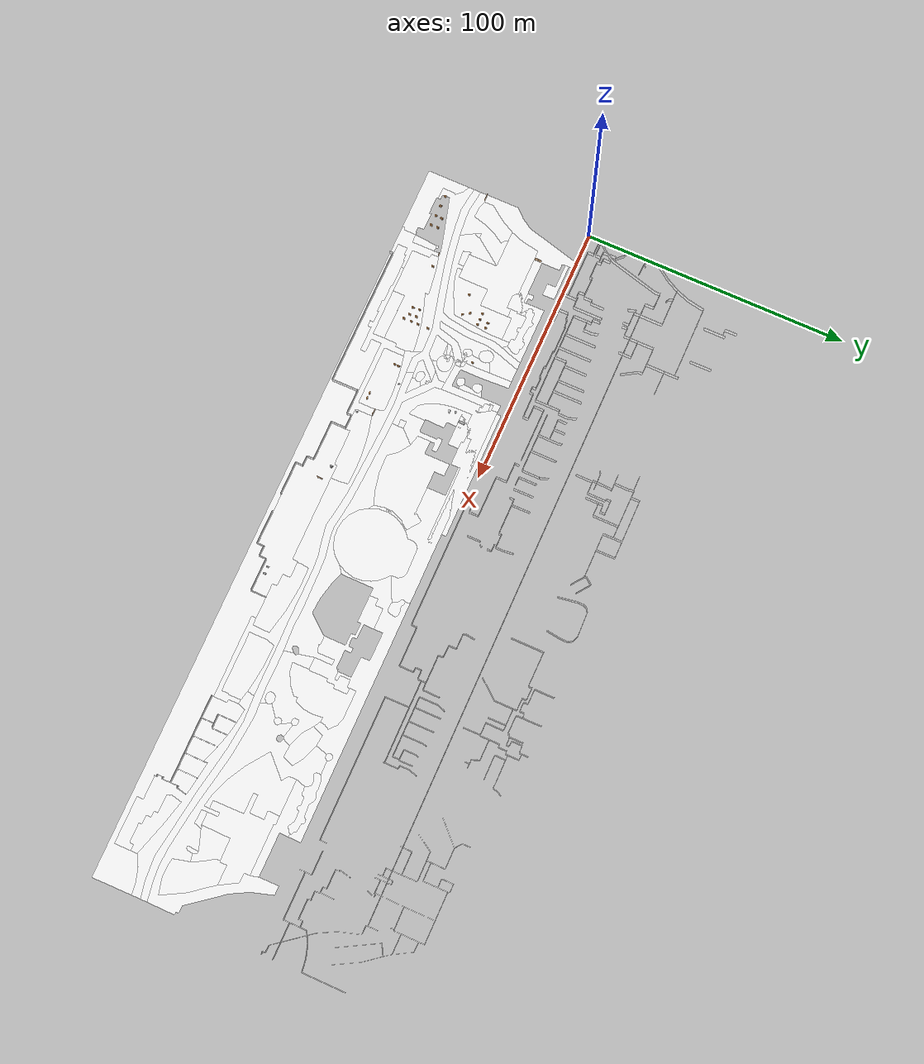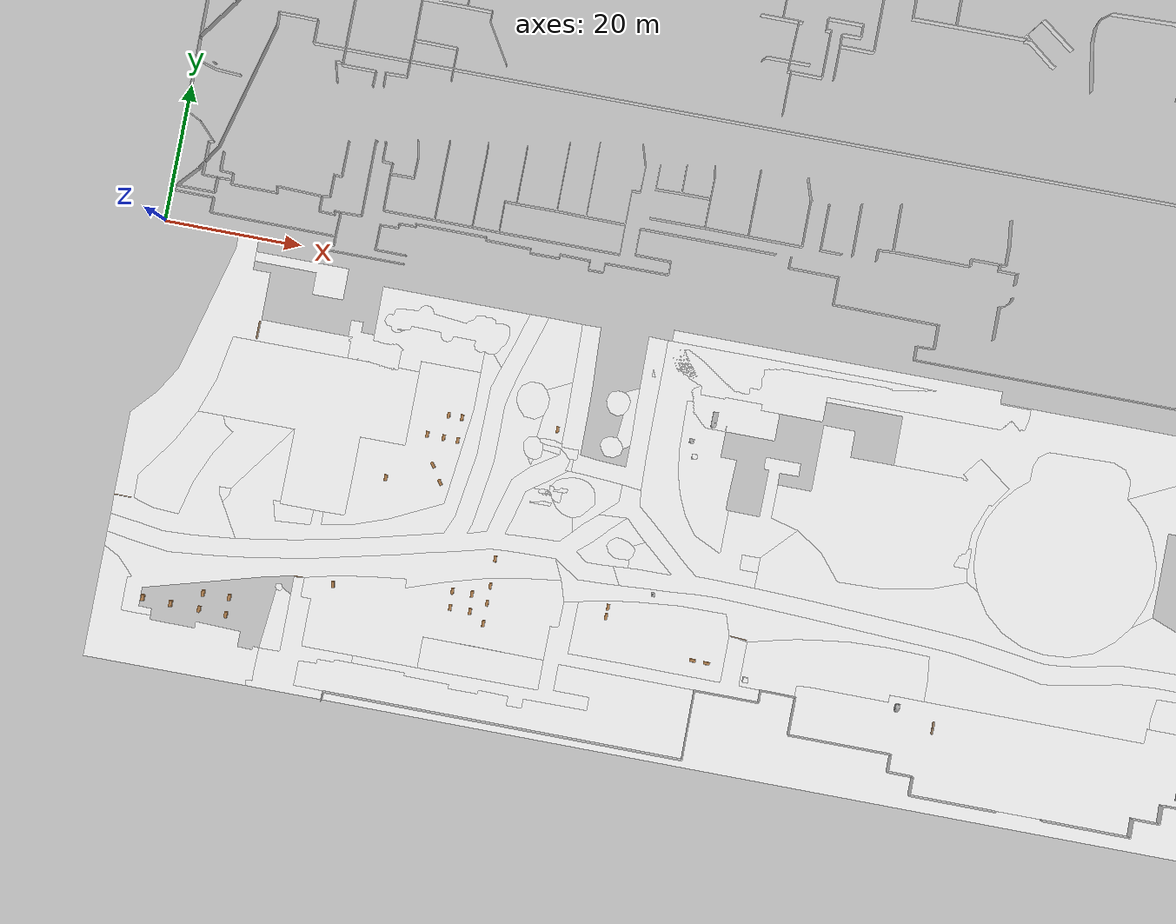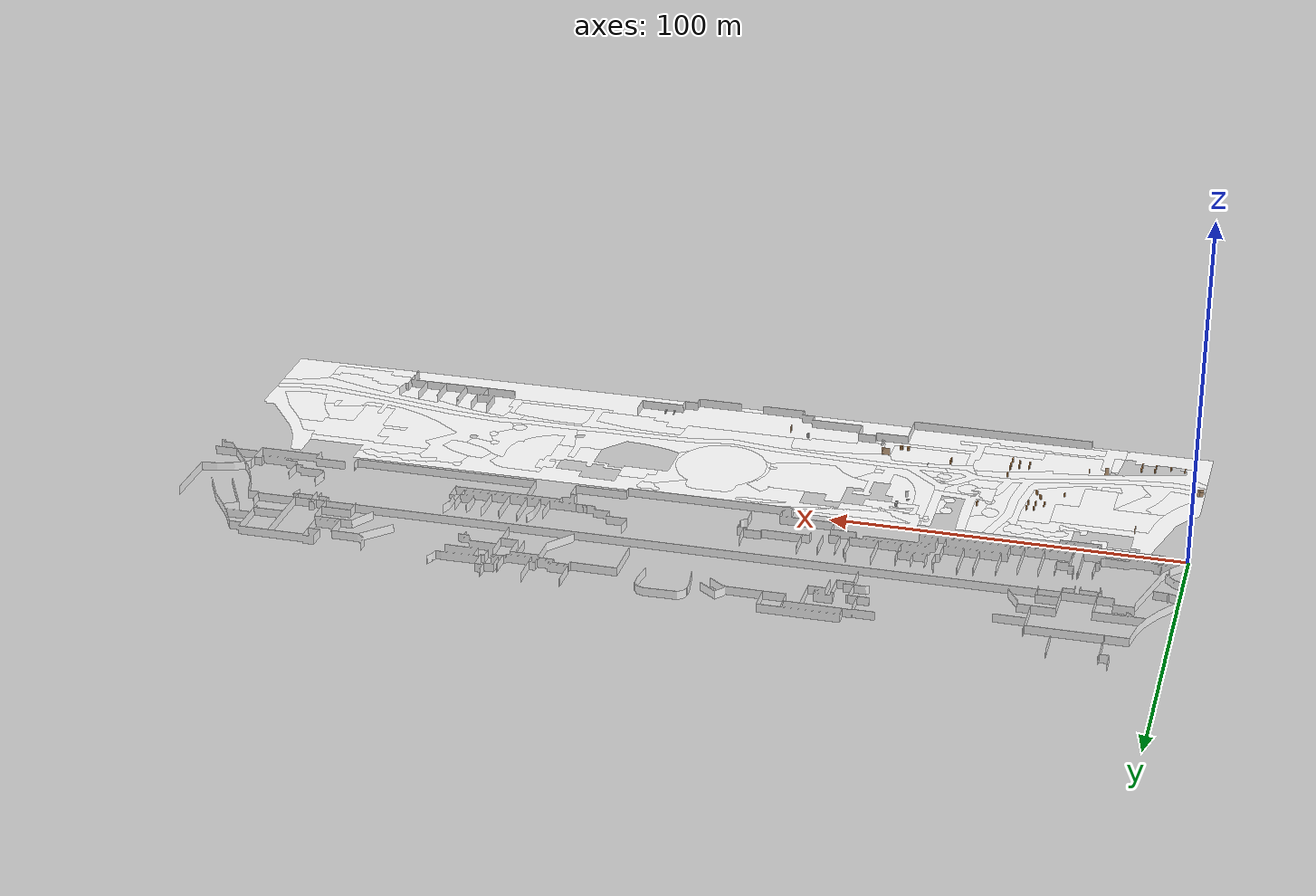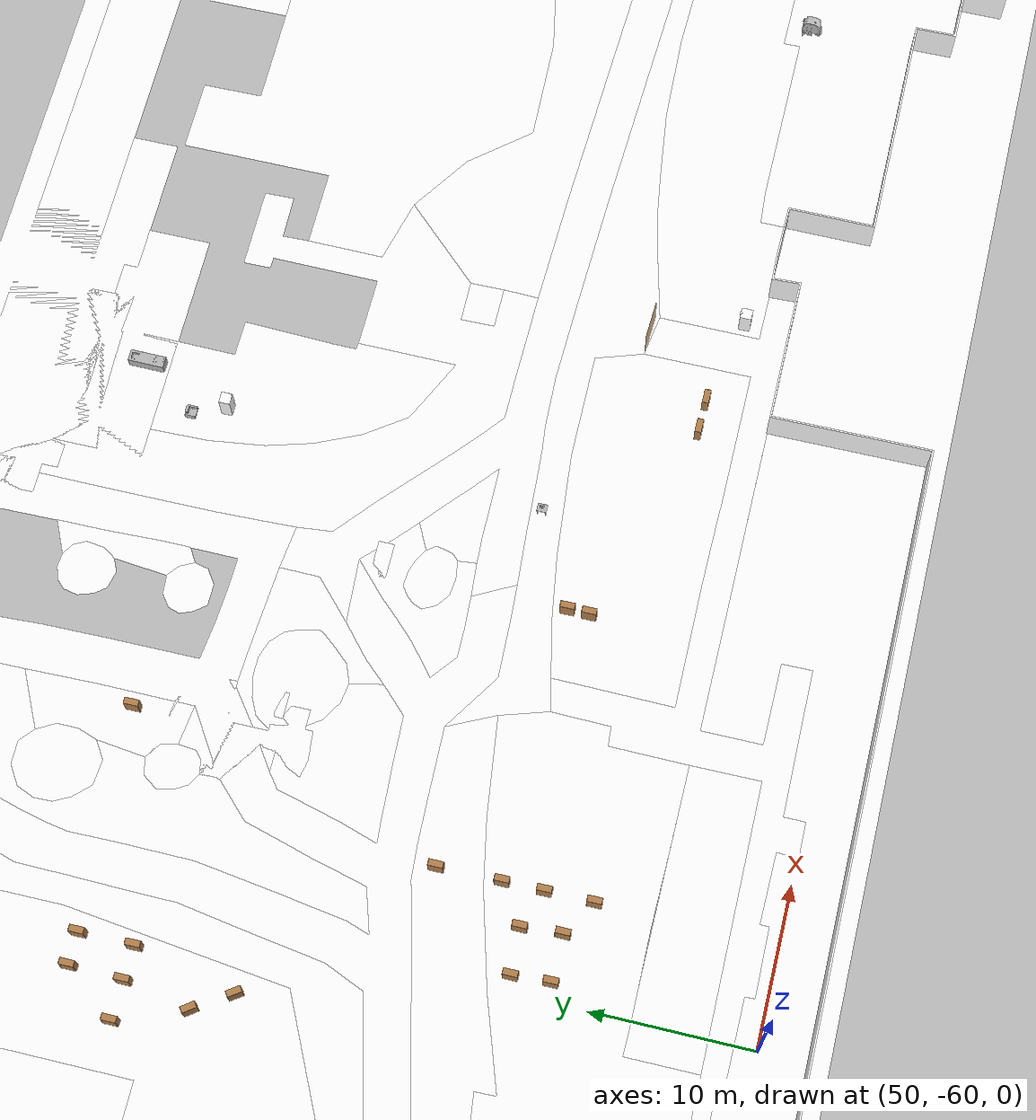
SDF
<sdf version="1.7">
 <world name="sim_world">
  <physics name="10ms" type="ode">
   <max_step_size>0.01</max_step_size>
   <real_time_factor>1.0</real_time_factor>
  </physics>
  <plugin filename="libignition-gazebo-physics-system.so" name="ignition::gazebo::systems::Physics"/>
  <plugin filename="libignition-gazebo-user-commands-system.so" name="ignition::gazebo::systems::UserCommands"/>
  <plugin filename="libignition-gazebo-scene-broadcaster-system.so" name="ignition::gazebo::systems::SceneBroadcaster"/>
  <scene><ambient>1 1 1</ambient><background>0.8 0.8 0.8</background><grid>false</grid></scene>
  <light type="directional" name="sun">
   <pose>0 0 10 0 0 0</pose>
   <diffuse>1 1 1 1</diffuse>
   <specular>0.2 0.2 0.2 1</specular>
   <attenuation>
    <range>1000</range>
    <constant>0.09</constant>
    <linear>0.001</linear>
    <quadratic>0.001</quadratic>
   </attenuation>
   <direction>-0.5 0.1 -0.9</direction>
  </light>
  <include>
   <name>Fridge</name>
   <uri>model://Fridge</uri>
   <pose>81.89234267903652 -19.580975229470475 0.0 0 0 -0.0006</pose>
   <static>True</static>
  </include>
  <include>
   <name>Bookshelf</name>
   <uri>model://Bookshelf</uri>
   <pose>61.473724341753524 -19.398828914457916 0.0 0 0 1.5708</pose>
   <static>True</static>
  </include>
  <include>
   <name>KitchenCountertop</name>
   <uri>model://KitchenCountertop</uri>
   <pose>83.79026129321836 -13.78234975470173 0.0 0 0 -0.0098</pose>
   <static>True</static>
  </include>
  <include>
   <name>MiniSofa</name>
   <uri>model://MiniSofa</uri>
   <pose>81.10438330457954 -17.398997055492206 0.0 0 0 1.5708</pose>
   <static>True</static>
  </include>
  <include>
   <name>Bookshelf_2</name>
   <uri>model://Bookshelf</uri>
   <pose>43.02299245471673 -23.55066446364193 0.0 0 0 1.5708</pose>
   <static>True</static>
  </include>
  <include>
   <name>Bookshelf_3</name>
   <uri>model://Bookshelf</uri>
   <pose>45.54725459667171 -20.259548268671924 0.0 0 0 1.5708</pose>
   <static>True</static>
  </include>
  <include>
   <name>Bookshelf_4</name>
   <uri>model://Bookshelf</uri>
   <pose>45.43294094901731 -23.592792984652505 0.0 0 0 1.5708</pose>
   <static>True</static>
  </include>
  <include>
   <name>Bookshelf_5</name>
   <uri>model://Bookshelf</uri>
   <pose>47.528116302901665 -20.240495994062854 0.0 0 0 1.5708</pose>
   <static>True</static>
  </include>
  <include>
   <name>Bookshelf_6</name>
   <uri>model://Bookshelf</uri>
   <pose>47.5090640282926 -23.63089753387064 0.0 0 0 1.5708</pose>
   <static>True</static>
  </include>
  <include>
   <name>Bookshelf_7</name>
   <uri>model://Bookshelf</uri>
   <pose>38.268382355400966 -30.849656563874845 0.0 0 0 1.5708</pose>
   <static>True</static>
  </include>
  <include>
   <name>Bookshelf_8</name>
   <uri>model://Bookshelf</uri>
   <pose>44.693515601689484 -27.89409034326973 0.0 0 0 2.1996</pose>
   <static>True</static>
  </include>
  <include>
   <name>Bookshelf_9</name>
   <uri>model://Bookshelf</uri>
   <pose>46.1584876997549 -30.181430880711083 0.0 0 0 2.188</pose>
   <static>True</static>
  </include>
  <include>
   <name>Bookshelf_10</name>
   <uri>model://Bookshelf</uri>
   <pose>89.11742509328596 -48.86793466603511 0.0 0 0 3.1321</pose>
   <static>True</static>
  </include>
  <include>
   <name>Bookshelf_11</name>
   <uri>model://Bookshelf</uri>
   <pose>87.05370241688124 -48.837138963542 0.0 0 0 3.1357</pose>
   <static>True</static>
  </include>
  <include>
   <name>LampAndStand</name>
   <uri>model://LampAndStand</uri>
   <pose>79.68695977116349 -40.3403172191372 0.0 0 0 1.5708</pose>
   <static>True</static>
  </include>
  <include>
   <name>Bookshelf_12</name>
   <uri>model://Bookshelf</uri>
   <pose>56.071911758842624 -43.45585684895984 0.0 0 0 1.5708</pose>
   <static>True</static>
  </include>
  <include>
   <name>Bookshelf_13</name>
   <uri>model://Bookshelf</uri>
   <pose>56.071911758842624 -45.999499753017155 0.0 0 0 1.5708</pose>
   <static>True</static>
  </include>
  <include>
   <name>Bookshelf_14</name>
   <uri>model://Bookshelf</uri>
   <pose>56.071911758842624 -48.997358738379475 0.0 0 0 1.5708</pose>
   <static>True</static>
  </include>
  <include>
   <name>Bookshelf_15</name>
   <uri>model://Bookshelf</uri>
   <pose>50.807817557480895 -45.22188773459788 0.0 0 0 1.5708</pose>
   <static>True</static>
  </include>
  <include>
   <name>Bookshelf_16</name>
   <uri>model://Bookshelf</uri>
   <pose>50.932642804919624 -47.59373167968031 0.0 0 0 1.5708</pose>
   <static>True</static>
  </include>
  <include>
   <name>Bookshelf_17</name>
   <uri>model://Bookshelf</uri>
   <pose>53.67896249231824 -45.09706248715915 0.0 0 0 1.5708</pose>
   <static>True</static>
  </include>
  <include>
   <name>Bookshelf_18</name>
   <uri>model://Bookshelf</uri>
   <pose>53.85733120115832 -47.629372572699005 0.0 0 0 1.5574</pose>
   <static>True</static>
  </include>
  <include>
   <name>Bookshelf_19</name>
   <uri>model://Bookshelf</uri>
   <pose>56.041608787589404 -39.48904188035441 0.0 0 0 1.5708</pose>
   <static>True</static>
  </include>
  <include>
   <name>Bookshelf_20</name>
   <uri>model://Bookshelf</uri>
   <pose>73.37975353495524 -44.71790579806402 0.0 0 0 1.5708</pose>
   <static>True</static>
  </include>
  <include>
   <name>Bookshelf_21</name>
   <uri>model://Bookshelf</uri>
   <pose>73.41383411238094 -43.3534508729361 0.0 0 0 1.5708</pose>
   <static>True</static>
  </include>
  <include>
   <name>Bookshelf_22</name>
   <uri>model://Bookshelf</uri>
   <pose>34.02087482380503 -47.4250533518914 0.0 0 0 -1.4328</pose>
   <static>True</static>
  </include>
  <include>
   <name>Bookshelf_23</name>
   <uri>model://Bookshelf</uri>
   <pose>6.880827521313181 -54.438014967368346 0.0 0 0 1.5708</pose>
   <static>True</static>
  </include>
  <include>
   <name>Bookshelf_24</name>
   <uri>model://Bookshelf</uri>
   <pose>10.997597030591715 -54.531223293580815 0.0 0 0 1.5708</pose>
   <static>True</static>
  </include>
  <include>
   <name>Bookshelf_25</name>
   <uri>model://Bookshelf</uri>
   <pose>15.352191484990348 -52.17736403875435 0.0 0 0 1.5708</pose>
   <static>True</static>
  </include>
  <include>
   <name>Bookshelf_26</name>
   <uri>model://Bookshelf</uri>
   <pose>19.196891227976447 -52.11199502759565 0.0 0 0 1.5708</pose>
   <static>True</static>
  </include>
  <include>
   <name>Bookshelf_27</name>
   <uri>model://Bookshelf</uri>
   <pose>15.207492744209404 -54.575733348917524 0.0 0 0 1.5708</pose>
   <static>True</static>
  </include>
  <include>
   <name>Bookshelf_28</name>
   <uri>model://Bookshelf</uri>
   <pose>19.159854263111406 -54.633875635224506 0.0 0 0 1.5708</pose>
   <static>True</static>
  </include>
  <include>
   <name>Fridge_2</name>
   <uri>model://Fridge</uri>
   <pose>95.01894927531835 -49.95498190310512 0.0 0 0 1.5708</pose>
   <static>True</static>
  </include>
  <include>
   <name>mopcart_dispenser</name>
   <uri>model://TeleportDispenser</uri>
   <pose>23.346427364707647 -36.437475189844115 0.0 0 0 1.5708</pose>
   <static>True</static>
  </include>
  <include>
   <name>mopcart_collector</name>
   <uri>model://TeleportIngestor</uri>
   <pose>26.063183177712883 -48.37701010735832 0.0 0 0 1.5708</pose>
   <static>True</static>
  </include>
  <include>
   <name>cleanerBotE_0</name>
   <uri>model://CleanerBotE</uri>
   <pose>159.69854730754096 -55.561195828696945 0.0 0 0 1.5709567322986409</pose>
  </include>
  <include>
   <name>cleanerBotE_1</name>
   <uri>model://CleanerBotE</uri>
   <pose>162.2735607672046 -55.57663474088015 0.0 0 0 1.5623100599110562</pose>
  </include>
  <include>
   <name>cleanerBotA_0</name>
   <uri>model://CleanerBotA</uri>
   <pose>117.41259866582594 -49.48039959721802 0.0 0 0 -1.5730303359239728</pose>
  </include>
  <model name="n02_door">
   <pose>16.32952389931159 -13.189019220001205 0.0 0 0 1.5676337427711504</pose>
   <link name="right">
    <pose>0.6621519759371044 0 1.11 0 0 0</pose>
    <visual name="right_visual">
     <geometry><box><size>1.3143039518742088 0.03 2.2</size></box></geometry>
     <material>
      <ambient>0.5 0.25 0 0.6</ambient>
      <diffuse>0.5 0.25 0 0.6</diffuse>
      <pbr><metal><metalness>0.0</metalness></metal></pbr>
     </material>
    </visual>
    <collision name="right_collision">
     <geometry><box><size>1.3143039518742088 0.03 2.2</size></box></geometry>
     <surface><contact><collide_bitmask>0x02</collide_bitmask></contact></surface>
    </collision>
    <inertial>
     <mass>50.0</mass>
     <inertia><ixx>20.17041666666667</ixx><iyy>27.364145324634016</iyy><izz>7.201228657967344</izz></inertia>
    </inertial>
   </link>
   <joint name="right_joint" type="revolute">
    <parent>world</parent>
    <child>right</child>
    <axis><xyz>0 0 1</xyz><limit><lower>0</lower><upper>1.6572222222222224</upper></limit></axis>
    <pose>0.6621519759371044 0 0 0 0 0</pose>
   </joint>
   <link name="left">
    <pose>-0.6621519759371044 0 1.11 0 0 0</pose>
    <visual name="left_visual">
     <geometry><box><size>1.3143039518742088 0.03 2.2</size></box></geometry>
     <material>
      <ambient>0.5 0.25 0 0.6</ambient>
      <diffuse>0.5 0.25 0 0.6</diffuse>
      <pbr><metal><metalness>0.0</metalness></metal></pbr>
     </material>
    </visual>
    <collision name="left_collision">
     <geometry><box><size>1.3143039518742088 0.03 2.2</size></box></geometry>
     <surface><contact><collide_bitmask>0x02</collide_bitmask></contact></surface>
    </collision>
    <inertial>
     <mass>50.0</mass>
     <inertia><ixx>20.17041666666667</ixx><iyy>27.364145324634016</iyy><izz>7.201228657967344</izz></inertia>
    </inertial>
   </link>
   <joint name="left_joint" type="revolute">
    <parent>world</parent>
    <child>left</child>
    <axis><xyz>0 0 1</xyz><limit><lower>-1.6572222222222224</lower><upper>0</upper></limit></axis>
    <pose>-0.6621519759371044 0 0 0 0 0</pose>
   </joint>
   <plugin name="door" filename="libdoor.so">
    <v_max_door>0.5</v_max_door>
    <a_max_door>0.3</a_max_door>
    <a_nom_door>0.15</a_nom_door>
    <dx_min_door>0.01</dx_min_door>
    <f_max_door>500.0</f_max_door>
    <door name="n02_door" type="DoubleSwingDoor" left_joint_name="left_joint" right_joint_name="right_joint"/>
   </plugin>
  </model>
  <model name="n01_door">
   <pose>1.5235249937389859 -40.44986779813934 0.0 0 0 3.134201392889213</pose>
   <link name="right">
    <pose>0.5888709777587251 0 1.11 0 0 0</pose>
    <visual name="right_visual">
     <geometry><box><size>1.1677419555174502 0.03 2.2</size></box></geometry>
     <material>
      <ambient>0.5 0.25 0 0.6</ambient>
      <diffuse>0.5 0.25 0 0.6</diffuse>
      <pbr><metal><metalness>0.0</metalness></metal></pbr>
     </material>
    </visual>
    <collision name="right_collision">
     <geometry><box><size>1.1677419555174502 0.03 2.2</size></box></geometry>
     <surface><contact><collide_bitmask>0x02</collide_bitmask></contact></surface>
    </collision>
    <inertial>
     <mass>50.0</mass>
     <inertia><ixx>20.17041666666667</ixx><iyy>25.8484219778155</iyy><izz>5.685505311148828</izz></inertia>
    </inertial>
   </link>
   <joint name="right_joint" type="revolute">
    <parent>world</parent>
    <child>right</child>
    <axis><xyz>0 0 1</xyz><limit><lower>0</lower><upper>1.6572222222222224</upper></limit></axis>
    <pose>0.5888709777587251 0 0 0 0 0</pose>
   </joint>
   <link name="left">
    <pose>-0.5888709777587251 0 1.11 0 0 0</pose>
    <visual name="left_visual">
     <geometry><box><size>1.1677419555174502 0.03 2.2</size></box></geometry>
     <material>
      <ambient>0.5 0.25 0 0.6</ambient>
      <diffuse>0.5 0.25 0 0.6</diffuse>
      <pbr><metal><metalness>0.0</metalness></metal></pbr>
     </material>
    </visual>
    <collision name="left_collision">
     <geometry><box><size>1.1677419555174502 0.03 2.2</size></box></geometry>
     <surface><contact><collide_bitmask>0x02</collide_bitmask></contact></surface>
    </collision>
    <inertial>
     <mass>50.0</mass>
     <inertia><ixx>20.17041666666667</ixx><iyy>25.8484219778155</iyy><izz>5.685505311148828</izz></inertia>
    </inertial>
   </link>
   <joint name="left_joint" type="revolute">
    <parent>world</parent>
    <child>left</child>
    <axis><xyz>0 0 1</xyz><limit><lower>-1.6572222222222224</lower><upper>0</upper></limit></axis>
    <pose>-0.5888709777587251 0 0 0 0 0</pose>
   </joint>
   <plugin name="door" filename="libdoor.so">
    <v_max_door>0.5</v_max_door>
    <a_max_door>0.3</a_max_door>
    <a_nom_door>0.15</a_nom_door>
    <dx_min_door>0.01</dx_min_door>
    <f_max_door>500.0</f_max_door>
    <door name="n01_door" type="DoubleSwingDoor" left_joint_name="left_joint" right_joint_name="right_joint"/>
   </plugin>
  </model>
  <model name="s04_door">
   <pose>28.73390968072509 -47.274154409675184 0.0 0 0 -3.1081700415635134</pose>
   <plugin name="door" filename="libdoor.so">
    <v_max_door>0.5</v_max_door>
    <a_max_door>0.3</a_max_door>
    <a_nom_door>0.15</a_nom_door>
    <dx_min_door>0.01</dx_min_door>
    <f_max_door>500.0</f_max_door>
    <door name="s04_door" type="SwingDoor" left_joint_name="left_joint" right_joint_name="empty_joint"/>
   </plugin>
   <link name="left">
    <pose>0 0 1.11 0 0 0</pose>
    <visual name="left_visual">
     <geometry><box><size>1.2015636603492745 0.03 2.2</size></box></geometry>
     <material>
      <ambient>0.5 0.25 0 0.6</ambient>
      <diffuse>0.5 0.25 0 0.6</diffuse>
      <pbr><metal><metalness>0.0</metalness></metal></pbr>
     </material>
    </visual>
    <collision name="left_collision">
     <geometry><box><size>1.2015636603492745 0.03 2.2</size></box></geometry>
     <surface><contact><collide_bitmask>0x02</collide_bitmask></contact></surface>
    </collision>
    <inertial>
     <mass>50.0</mass>
     <inertia><ixx>20.17041666666667</ixx><iyy>26.182313457799783</iyy><izz>6.019396791133111</izz></inertia>
    </inertial>
   </link>
   <joint name="left_joint" type="revolute">
    <parent>world</parent>
    <child>left</child>
    <axis><xyz>0 0 1</xyz><limit><lower>-1.6572222222222224</lower><upper>0</upper></limit></axis>
    <pose>0.6057818301746373 0 0 0 0 0</pose>
   </joint>
  </model>
  <model name="s08_door">
   <pose>93.01533981018017 -44.236384193881804 0.0 0 0 -0.04792369781717709</pose>
   <plugin name="door" filename="libdoor.so">
    <v_max_door>0.5</v_max_door>
    <a_max_door>0.3</a_max_door>
    <a_nom_door>0.15</a_nom_door>
    <dx_min_door>0.01</dx_min_door>
    <f_max_door>500.0</f_max_door>
    <door name="s08_door" type="SwingDoor" left_joint_name="empty_joint" right_joint_name="right_joint"/>
   </plugin>
   <link name="right">
    <pose>0 0 1.11 0 0 0</pose>
    <visual name="right_visual">
     <geometry><box><size>2.4328097402213444 0.03 2.2</size></box></geometry>
     <material>
      <ambient>0.5 0.25 0 0.6</ambient>
      <diffuse>0.5 0.25 0 0.6</diffuse>
      <pbr><metal><metalness>0.0</metalness></metal></pbr>
     </material>
    </visual>
    <collision name="right_collision">
     <geometry><box><size>2.4328097402213444 0.03 2.2</size></box></geometry>
     <surface><contact><collide_bitmask>0x02</collide_bitmask></contact></surface>
    </collision>
    <inertial>
     <mass>50.0</mass>
     <inertia><ixx>20.17041666666667</ixx><iyy>44.8273468004827</iyy><izz>24.664430133816023</izz></inertia>
    </inertial>
   </link>
   <joint name="right_joint" type="revolute">
    <parent>world</parent>
    <child>right</child>
    <axis><xyz>0 0 1</xyz><limit><lower>0</lower><upper>1.57</upper></limit></axis>
    <pose>1.2214048701106721 0 0 0 0 0</pose>
   </joint>
  </model>
  <model name="zone_4_door">
   <pose>122.95221175215931 -51.78087963438976 0.0 0 0 1.576711873276658</pose>
   <link name="right">
    <pose>-0.4720037254296668 0 1.11 0 0 0</pose>
    <visual name="right_visual">
     <geometry><box><size>0.9340074508593336 0.03 2.2</size></box></geometry>
     <material>
      <ambient>0.5 0.25 0 0.6</ambient>
      <diffuse>0.5 0.25 0 0.6</diffuse>
      <pbr><metal><metalness>0.0</metalness></metal></pbr>
     </material>
    </visual>
    <collision name="right_collision">
     <geometry><box><size>0.9340074508593336 0.03 2.2</size></box></geometry>
     <surface><contact><collide_bitmask>0x02</collide_bitmask></contact></surface>
    </collision>
    <inertial>
     <mass>50.0</mass>
     <inertia><ixx>20.17041666666667</ixx><iyy>23.801541326086465</iyy><izz>3.6386246594197935</izz></inertia>
    </inertial>
   </link>
   <joint name="right_joint" type="revolute">
    <parent>world</parent>
    <child>right</child>
    <axis><xyz>0 0 1</xyz><limit><lower>0</lower><upper>1.57</upper></limit></axis>
    <pose>-0.4720037254296668 0 0 0 0 0</pose>
   </joint>
   <link name="left">
    <pose>0.4720037254296668 0 1.11 0 0 0</pose>
    <visual name="left_visual">
     <geometry><box><size>0.9340074508593336 0.03 2.2</size></box></geometry>
     <material>
      <ambient>0.5 0.25 0 0.6</ambient>
      <diffuse>0.5 0.25 0 0.6</diffuse>
      <pbr><metal><metalness>0.0</metalness></metal></pbr>
     </material>
    </visual>
    <collision name="left_collision">
     <geometry><box><size>0.9340074508593336 0.03 2.2</size></box></geometry>
     <surface><contact><collide_bitmask>0x02</collide_bitmask></contact></surface>
    </collision>
    <inertial>
     <mass>50.0</mass>
     <inertia><ixx>20.17041666666667</ixx><iyy>23.801541326086465</iyy><izz>3.6386246594197935</izz></inertia>
    </inertial>
   </link>
   <joint name="left_joint" type="revolute">
    <parent>world</parent>
    <child>left</child>
    <axis><xyz>0 0 1</xyz><limit><lower>-1.57</lower><upper>0</upper></limit></axis>
    <pose>0.4720037254296668 0 0 0 0 0</pose>
   </joint>
   <plugin name="door" filename="libdoor.so">
    <v_max_door>0.5</v_max_door>
    <a_max_door>0.3</a_max_door>
    <a_nom_door>0.15</a_nom_door>
    <dx_min_door>0.01</dx_min_door>
    <f_max_door>500.0</f_max_door>
    <door name="zone_4_door" type="DoubleSwingDoor" left_joint_name="left_joint" right_joint_name="right_joint"/>
   </plugin>
  </model>
  <include><name>airport_terminal_L1</name><uri>model://airport_terminal_L1</uri></include>
  <rmf_charger_waypoints name="charger_waypoints">
   <rmf_vertex name="charger_tinyRobot_3" x="267.0690369387946" y="-61.44563866107981" level="L1"/>
   <rmf_vertex name="charger_tinyRobot_2" x="265.0190286152335" y="-61.44563866107981" level="L1"/>
   <rmf_vertex name="charger_tinyRobot_1" x="262.8078150543551" y="-61.44563866107981" level="L1"/>
   <rmf_vertex name="charger_tinyRobot_0" x="260.3432555143001" y="-61.4225624146783" level="L1"/>
   <rmf_vertex name="n03" x="21.776503512545712" y="-27.451042836735567" level="L1"/>
   <rmf_vertex name="charger_deliveryRobot_0" x="12.14664628201452" y="-1.7813876759479343" level="L1"/>
   <rmf_vertex name="charger_deliveryRobot_1" x="15.053432109870556" y="-6.301950436316086" level="L1"/>
   <rmf_vertex name="charger_deliveryRobot_2" x="14.776845640545796" y="-9.279278953349664" level="L1"/>
   <rmf_vertex name="n13" x="86.4971624814258" y="-9.632567252350587" level="L1"/>
   <rmf_vertex name="s08" x="96.59527863359884" y="-51.964504143122" level="L1"/>
   <rmf_vertex name="s11" x="152.34773630524631" y="-44.31862925000672" level="L1"/>
   <rmf_vertex name="s03" x="28.719661535704944" y="-51.1928870214547" level="L1"/>
   <rmf_vertex name="s07" x="67.96710086476676" y="-49.36132288091133" level="L1"/>
   <rmf_vertex name="charger_cleanerBotE_0" x="159.69854730754096" y="-55.561195828696945" level="L1"/>
   <rmf_vertex name="charger_cleanerBotE_1" x="162.2735607672046" y="-55.57663474088015" level="L1"/>
   <rmf_vertex name="charger_cleanerBotA_0" x="117.41259866582594" y="-49.48039959721802" level="L1"/>
  </rmf_charger_waypoints>
  <plugin filename="libcrowd_simulator.so" name="crowd_simulation">
   <behavior_file>behavior_file.xml</behavior_file>
   <scene_file>scene_file.xml</scene_file>
   <update_time_step>0.1</update_time_step>
   <model_type>
    <typename>human</typename>
    <animation>walk</animation>
    <animation_speed>1</animation_speed>
    <filename>model://MaleVisitorPhone</filename>
    <initial_pose>0 0 0 0 0 0</initial_pose>
   </model_type>
   <external_agent>tinyRobot_4</external_agent>
   <external_agent>deliveryRobot_2</external_agent>
   <external_agent>tinyRobot_2</external_agent>
   <external_agent>deliveryRobot_0</external_agent>
   <external_agent>deliveryRobot_1</external_agent>
   <external_agent>tinyRobot_0</external_agent>
   <external_agent>tinyRobot_1</external_agent>
   <external_agent>cleanerBotE_0</external_agent>
   <external_agent>cleanerBotE_1</external_agent>
   <external_agent>cleanerBotA_0</external_agent>
   <external_agent>caddy</external_agent>
  </plugin>
 </world>
</sdf>

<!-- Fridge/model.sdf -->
<sdf version="1.6">
  <model name="Fridge">
    <static>true</static>
    <link name="base_link">
      <visual name="visual">
        <geometry>
          <mesh>
            <uri>meshes/fridge.dae</uri>
          </mesh>
        </geometry>
        <material>
          <diffuse>1.0 1.0 1.0</diffuse>
          <specular>1.0 1.0 1.0</specular>
          <pbr>
            <metal>
              <albedo_map>materials/textures/Fridge_Albedo.jpg</albedo_map>
              <normal_map>materials/textures/Fridge_Normal.png</normal_map>
              <roughness_map>materials/textures/Fridge_Roughness.jpg</roughness_map>
              <metalness_map>materials/textures/Fridge_Metalness.jpg</metalness_map>
            </metal>
          </pbr>
        </material>
      </visual>
      <collision name="Box001">
        <pose>0.0 0.0 0.867923 0.0 0.0 0.0</pose>
        <geometry>
          <box>
            <size>0.734673 0.7239 1.73585</size>
          </box>
        </geometry>
      </collision>
    </link>
  </model>
</sdf>

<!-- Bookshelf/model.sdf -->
<sdf version="1.5">
  <model name="Bookshelf">
    <static>true</static>
    <link name="link">
      <inertial>
        <mass>1.0</mass>
      </inertial>
      <collision name="back">
        <pose>0 0.005 0.6 0 0 0</pose>
        <geometry>
          <box>
            <size>0.9 0.01 1.2</size>
          </box>
        </geometry>
      </collision>
      <visual name="visual1">
        <pose>0 0.005 0.6 0 0 0</pose>
        <geometry>
          <box>
            <size>0.9 0.01 1.2</size>
          </box>
        </geometry>
        <material>
          <diffuse>1.0 1.0 1.0</diffuse>
          <script>
            <uri>file://media/materials/scripts/gazebo.material</uri>
            <name>Gazebo/Wood</name>
          </script>
          <!-- PBR for Ignition, material scripts for gazebo classic-->
          <pbr>
            <metal>
              <albedo_map>model://Bookshelf/bookshelf_diffuse.jpg</albedo_map>
            </metal>
          </pbr>
        </material>
      </visual>
      <collision name="left_side">
        <pose>0.45 -0.195 0.6 0 0 0</pose>
        <geometry>
          <box>
            <size>0.02 0.4 1.2</size>
          </box>
        </geometry>
      </collision>
      <visual name="visual2">
        <pose>0.45 -0.195 0.6 0 0 0</pose>
        <geometry>
          <box>
            <size>0.02 0.4 1.2</size>
          </box>
        </geometry>
        <material>
          <diffuse>1.0 1.0 1.0</diffuse>
          <script>
            <uri>file://media/materials/scripts/gazebo.material</uri>
            <name>Gazebo/Wood</name>
          </script>
          <!-- PBR for Ignition, material scripts for gazebo classic-->
          <pbr>
            <metal>
              <albedo_map>model://Bookshelf/bookshelf_diffuse.jpg</albedo_map>
            </metal>
          </pbr>
        </material>
      </visual>
      <collision name="right_side">
        <pose>-0.45 -0.195 0.6 0 0 0</pose>
        <geometry>
          <box>
            <size>0.02 0.4 1.2</size>
          </box>
        </geometry>
      </collision>
      <visual name="visual3">
        <pose>-0.45 -0.195 0.6 0 0 0</pose>
        <geometry>
          <box>
            <size>0.02 0.4 1.2</size>
          </box>
        </geometry>
        <material>
          <diffuse>1.0 1.0 1.0</diffuse>
          <script>
            <uri>file://media/materials/scripts/gazebo.material</uri>
            <name>Gazebo/Wood</name>
          </script>
          <!-- PBR for Ignition, material scripts for gazebo classic-->
          <pbr>
            <metal>
              <albedo_map>model://Bookshelf/bookshelf_diffuse.jpg</albedo_map>
            </metal>
          </pbr>
        </material>
      </visual>
      <collision name="bottom">
        <pose>0 -0.195 0.03 0 0 0</pose>
        <geometry>
          <box>
            <size>0.88 0.4 0.06</size>
          </box>
        </geometry>
      </collision>
      <visual name="visual4">
        <pose>0 -0.195 0.03 0 0 0</pose>
        <geometry>
          <box>
            <size>0.88 0.4 0.06</size>
          </box>
        </geometry>
        <material>
          <diffuse>1.0 1.0 1.0</diffuse>
          <script>
            <uri>file://media/materials/scripts/gazebo.material</uri>
            <name>Gazebo/Wood</name>
          </script>
          <!-- PBR for Ignition, material scripts for gazebo classic-->
          <pbr>
            <metal>
              <albedo_map>model://Bookshelf/bookshelf_diffuse.jpg</albedo_map>
            </metal>
          </pbr>
        </material>
      </visual>
      <collision name="top">
        <pose>0 -0.195 1.19 0 0 0</pose>
        <geometry>
          <box>
            <size>0.88 0.4 0.02</size>
          </box>
        </geometry>
      </collision>
      <visual name="visual5">
        <pose>0 -0.195 1.19 0 0 0</pose>
        <geometry>
          <box>
            <size>0.88 0.4 0.02</size>
          </box>
        </geometry>
        <material>
          <diffuse>1.0 1.0 1.0</diffuse>
          <script>
            <uri>file://media/materials/scripts/gazebo.material</uri>
            <name>Gazebo/Wood</name>
          </script>
          <!-- PBR for Ignition, material scripts for gazebo classic-->
          <pbr>
            <metal>
              <albedo_map>model://Bookshelf/bookshelf_diffuse.jpg</albedo_map>
            </metal>
          </pbr>
        </material>
      </visual>
      <collision name="low_shelf">
        <pose>0 -0.195 0.43 0 0 0</pose>
        <geometry>
          <box>
            <size>0.88 0.4 0.02</size>
          </box>
        </geometry>
      </collision>
      <visual name="visual6">
        <pose>0 -0.195 0.43 0 0 0</pose>
        <geometry>
          <box>
            <size>0.88 0.4 0.02</size>
          </box>
        </geometry>
        <material>
          <diffuse>1.0 1.0 1.0</diffuse>
          <script>
            <uri>file://media/materials/scripts/gazebo.material</uri>
            <name>Gazebo/Wood</name>
          </script>
          <!-- PBR for Ignition, material scripts for gazebo classic-->
          <pbr>
            <metal>
              <albedo_map>model://Bookshelf/bookshelf_diffuse.jpg</albedo_map>
            </metal>
          </pbr>
        </material>
      </visual>
      <collision name="high_shelf">
        <pose>0 -0.195 0.8 0 0 0</pose>
        <geometry>
          <box>
            <size>0.88 0.4 0.02</size>
          </box>
        </geometry>
      </collision>
      <visual name="visual7">
        <pose>0 -0.195 0.8 0 0 0</pose>
        <geometry>
          <box>
            <size>0.88 0.4 0.02</size>
          </box>
        </geometry>
        <material>
          <diffuse>1.0 1.0 1.0</diffuse>
          <script>
            <uri>file://media/materials/scripts/gazebo.material</uri>
            <name>Gazebo/Wood</name>
          </script>
          <!-- PBR for Ignition, material scripts for gazebo classic-->
          <pbr>
            <metal>
              <albedo_map>model://Bookshelf/bookshelf_diffuse.jpg</albedo_map>
            </metal>
          </pbr>
        </material>
      </visual>
    </link>
  </model>
</sdf>

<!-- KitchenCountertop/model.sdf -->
<sdf version="1.5">
  <model name="KitchenCountertop">
    <link name="link">
      <pose>0 0 0 0 0 0</pose>

        <visual name="visual">
          <geometry>
            <mesh><uri>model://KitchenCountertop/meshes/Counter.obj</uri></mesh>
          </geometry>
        </visual>

        <collision name="collision">
          <geometry>
            <mesh><uri>model://KitchenCountertop/meshes/Counter.obj</uri></mesh>
          </geometry>
        </collision>

    </link>
  </model>
</sdf>

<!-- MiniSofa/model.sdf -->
<sdf version="1.6">
  <model name='MiniSofa'>
    <link name="body">
      <pose>0 0 0 0 0 -1.57079632679</pose>

      <visual name="visual">
        <geometry>
          <mesh>
            <uri>model://MiniSofa/meshes/minisofa.obj</uri>
            <scale>1.00 1.00 1.00</scale>
          </mesh>
        </geometry>
      </visual>

      <collision name="collision">
        <geometry>
          <mesh>
            <uri>model://MiniSofa/meshes/minisofa.obj</uri>
            <scale>1.00 1.00 1.00</scale>
          </mesh>
        </geometry>
      </collision>

    </link>
  </model>
</sdf>

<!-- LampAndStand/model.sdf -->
<sdf version="1.6">
  <model name="LampAndStand">
   <static>true</static>
    <link name="body">
      <pose>0 0 0 0 0 0</pose>

      <visual name="visual">
        <geometry>
          <mesh>
            <uri>model://LampAndStand/meshes/LampAndStand.obj</uri>
          </mesh>
        </geometry>
      </visual>

      <collision name="collision">
        <geometry>
          <mesh>
            <uri>model://LampAndStand/meshes/LampAndStand_Col.obj</uri>
          </mesh>
        </geometry>
      </collision>

    </link>
  </model>
</sdf>

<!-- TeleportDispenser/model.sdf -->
<sdf version="1.6">
  <model name="TeleportDispenser">
    <pose>0.0 0.0 0.0 0.0 0.0 0.0</pose>
    <static>true</static>

    <link name="visual_link">
      <pose>0.0 0.0 0.05 0.0 0.0 0.0</pose>
      <visual name="visual">
        <geometry>
          <box>
            <size>0.1 0.1 0.1</size>
          </box>
        </geometry>
        <material>
          <ambient>128 192 210 0.1</ambient>
          <diffuse>128 192 210 0.1</diffuse>
        </material>
      </visual>
    </link>

    <plugin name="teleport_dispenser" filename="libteleport_dispenser.so">
    </plugin>

  </model>
</sdf>

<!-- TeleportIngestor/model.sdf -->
<sdf version="1.6">
  <model name="TeleportIngestor">
    <pose>0.0 0.0 0.0 0.0 0.0 0.0</pose>
    <static>true</static>

    <link name="visual_link">
      <pose>0.0 0.0 0.05 0.0 0.0 0.0</pose>
      <visual name="visual">
        <geometry>
          <box>
            <size>0.1 0.1 0.1</size>
          </box>
        </geometry>
        <material>
          <ambient>128 192 210 0.1</ambient>
          <diffuse>128 192 210 0.1</diffuse>
        </material>
      </visual>
    </link>

    <plugin name="teleport_ingestor" filename="libteleport_ingestor.so">
    </plugin>

  </model>
</sdf>

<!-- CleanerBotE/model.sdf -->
<sdf version="1.6">
  <model name="CleanerBotE">

    <!-- TODO: Find actual physical properties for Avidbot instead of duplicating -->
    <!-- Note: rotational axis of the robot should located at the origin  -->

    <plugin name="slotcar" filename="libslotcar.so">

      <!-- Forward / Backward -->
      <nominal_drive_speed>0.7</nominal_drive_speed>
      <nominal_drive_acceleration>0.5</nominal_drive_acceleration>
      <max_drive_acceleration>0.6</max_drive_acceleration>

      <!-- Turning -->
      <nominal_turn_speed>0.4</nominal_turn_speed>
      <nominal_turn_acceleration>1.0</nominal_turn_acceleration>
      <max_turn_acceleration>1.2</max_turn_acceleration>

      <!-- Stop distance and radius  -->
      <stop_distance>1.5</stop_distance>
      <stop_radius>1.5</stop_radius>

      <!-- Battery params -->
      <nominal_voltage>24.0</nominal_voltage>
      <nominal_capacity>30.0</nominal_capacity>
      <charging_current>10.0</charging_current>

      <!-- Physical params -->
      <mass>70.0</mass>
      <inertia>40.0</inertia>
      <friction_coefficient>0.22</friction_coefficient>

      <!-- Power systems -->
      <nominal_power>100.0</nominal_power>
    </plugin>

    <!-- Main CleanerbotE Body -->

    <link name="body">
      <pose>0 0 0 0 0 0</pose>

      <inertial>
        <pose>0.36 0 0.43294142 0 0 0</pose>
        <mass>10.0</mass> <!-- Mass reduced to prevent model rolling when stationary -->
        <inertia>
          <ixx>2.441</ixx>
          <iyy>3.2373</iyy>
          <izz>2.332</izz>
        </inertia>
      </inertial>

      <visual name="visual">
        <pose>0.35 0 0 0 0 0</pose>
        <geometry>
          <mesh>
            <uri>model://CleanerBotE/meshes/CleanerBotE.obj</uri>
          </mesh>
        </geometry>
      </visual>
      <collision name="body_collision">
        <pose>0.35 0 0.04 0 0 0</pose>
        <geometry>
          <mesh>
            <uri>model://CleanerBotE/meshes/CleanerBotE_Col.obj</uri>
          </mesh>
        </geometry>
      </collision>

      <collision name="front_virtual_wheel_collision">
        <pose>0.7 0.0 0.09 0 0 0</pose>
        <geometry>
          <sphere>
            <radius>0.1</radius>
          </sphere>
        </geometry>
        <surface>
          <contact>
            <ode>
              <kp>1e+08</kp>
              <min_depth>0.005</min_depth>
            </ode>
          </contact>
          <friction>
            <ode>
              <mu>0</mu>
              <mu2>0</mu2>
            </ode>
          </friction>
        </surface>
      </collision>
    </link>

    <!-- Left wheel link and revolute joint -->

    <link name="tire_left">
      <pose>0 0.20 0.08 0 0 0</pose>

      <inertial>
        <pose>0 0 0 0 0 0</pose>
        <mass>3.0</mass>
        <inertia>
          <ixx>0.757897446874</ixx>
          <iyy>1.302975553365</iyy>
          <izz>0.757897446874</izz>
        </inertia>
      </inertial>

      <visual name="tire_left">
        <geometry>
          <mesh>
            <uri>model://CleanerBotE/meshes/CleanerBotE_Wheel.obj</uri>
          </mesh>
        </geometry>
      </visual>

      <collision name='tire_left_collision'>
        <geometry>
          <sphere>
            <radius>0.09</radius>
          </sphere>
        </geometry>
        <surface>
          <contact>
            <ode>
              <kp>10000000.0</kp>
              <kd>1.0</kd>
            </ode>
          </contact>
        </surface>
      </collision>
    </link>

    <joint name="joint_tire_left" type="revolute">
      <parent>body</parent>
      <child>tire_left</child>
      <axis>
        <xyz>0 1 0</xyz>
      </axis>
    </joint>

    <!-- Right wheel link and revolute joint -->

    <link name="tire_right">
      <pose>0 -0.20 0.08 0 0 0</pose>
      <inertial>
        <pose>0 0 0 0 0 0</pose>
        <mass>3.0</mass>
        <inertia>
          <ixx>0.657897446874</ixx>
          <iyy>1.102975553365</iyy>
          <izz>0.657897446874</izz>
        </inertia>
      </inertial>

      <visual name="tire_right">
        <geometry>
          <mesh>
            <uri>model://CleanerBotE/meshes/CleanerBotE_Wheel.obj</uri>
          </mesh>
        </geometry>
      </visual>

      <collision name='tire_right_collision'>
        <geometry>
          <sphere>
            <radius>0.09</radius>
          </sphere>
        </geometry>
        <surface>
          <contact>
            <ode>
              <kp>10000000.0</kp>
              <kd>1.0</kd>
            </ode>
          </contact>
        </surface>
      </collision>
    </link>

    <joint name="joint_tire_right" type="revolute">
      <parent>body</parent>
      <child>tire_right</child>
      <axis>
        <xyz>0 1 0</xyz>
      </axis>
    </joint>

  </model>
</sdf>

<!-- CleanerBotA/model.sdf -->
<sdf version="1.6">
  <model name='CleanerBotA'>

    <!-- TODO: Find actual physical properties for CleanerBotA instead of duplicating -->
    <!-- Note: rotational axis of the robot should located at the origin  -->

    <plugin name="slotcar" filename="libslotcar.so">

      <!-- Forward / Backward -->
      <nominal_drive_speed>0.7</nominal_drive_speed>
      <nominal_drive_acceleration>0.5</nominal_drive_acceleration>
      <max_drive_acceleration>0.6</max_drive_acceleration>

      <!-- Turning -->
      <nominal_turn_speed>0.4</nominal_turn_speed>
      <nominal_turn_acceleration>1.0</nominal_turn_acceleration>
      <max_turn_acceleration>1.2</max_turn_acceleration>

      <!-- Stop distance and radius  -->
      <stop_distance>1.5</stop_distance>
      <stop_radius>1.5</stop_radius>

      <!-- Can the robot drive backwards -->
      <reversible>false</reversible>

      <!-- Battery params -->
      <nominal_voltage>24.0</nominal_voltage>
      <nominal_capacity>20.0</nominal_capacity>
      <charging_current>10.0</charging_current>

      <!-- Physical params -->
      <mass>70.0</mass>
      <inertia>40.0</inertia>
      <friction_coefficient>0.22</friction_coefficient>

      <!-- Power systems -->
      <nominal_power>100.0</nominal_power>

    </plugin>

    <!-- Main CleanerBotA Body -->

    <link name="body">
      <pose>0 0 0 0 0 0</pose>

      <inertial>
        <pose>0.36 0 0.43294142 0 0 0</pose>
        <mass>15.0</mass> <!-- Mass reduced to prevent model rolling when stationary -->
        <inertia>
          <ixx>3.016</ixx>
          <iyy>2.332</iyy>
          <izz>2.425</izz>
        </inertia>
      </inertial>

      <visual name="visual">
        <pose frame=''>0.36 0 0 0 0 0</pose>
        <geometry>
          <mesh><uri>model://CleanerBotA/meshes/CleanerBotA.obj</uri></mesh>
        </geometry>
      </visual>
      <collision name="body_collision">
        <pose frame=''>0.46 0 0.7 0 0 0</pose>
        <geometry>
          <box>
            <size>1.3 0.8 1.2</size>
          </box>
        </geometry>
      </collision>

      <visual name="WheelFront">
        <pose>0.86 0.0 0.07 0 0 0</pose>
        <geometry>
          <mesh>
            <uri>model://CleanerBotA/meshes/CleanerBotA_WheelFront.obj</uri>
          </mesh>
        </geometry>
      </visual>
      <collision name='front_wheel_collision'>
        <pose>0.86 0.0 0.06 0 0 0</pose>
        <geometry>
          <sphere>
            <radius>0.1</radius>
          </sphere>
        </geometry>
        <surface>
          <contact>
            <ode>
              <kp>1e+08</kp>
              <min_depth>0.005</min_depth>
            </ode>
          </contact>
          <friction>
            <ode>
              <mu>0</mu>
              <mu2>0</mu2>
            </ode>
          </friction>
        </surface>
      </collision>

    </link>

    <!-- Left wheel link and revolute joint -->

    <link name="tire_left">
      <pose>0 0.26 0.08 0 0 0</pose>

      <inertial>
        <pose>0 0 0 0 0 0</pose>
        <mass>5.0</mass>
        <inertia>
          <ixx>0.02</ixx>
          <iyy>0.02</iyy>
          <izz>0.02</izz>
        </inertia>
      </inertial>

      <visual name="tire_left">
        <geometry>
          <mesh>
            <uri>model://CleanerBotA/meshes/CleanerBotA_WheelBack.obj</uri>
          </mesh>
        </geometry>
      </visual>

      <collision name='tire_left_collision'>
        <geometry>
          <sphere>
            <radius>0.1</radius>
          </sphere>
        </geometry>
        <surface>
          <contact>
            <ode>
              <kp>10000000.0</kp>
              <kd>1.0</kd>
            </ode>
          </contact>
        </surface>
      </collision>
    </link>

    <joint name="joint_tire_left" type="revolute">
      <parent>body</parent>
      <child>tire_left</child>
      <axis>
        <xyz>0 1 0</xyz>
      </axis>
    </joint>

    <!-- Right wheel link and revolute joint -->

    <link name="tire_right">
      <pose>0 -0.26 0.08 0 0 0</pose>
      <inertial>
        <pose>0 0 0 0 0 0</pose>
        <mass>5.0</mass>
        <inertia>
          <ixx>0.02</ixx>
          <iyy>0.02</iyy>
          <izz>0.02</izz>
        </inertia>
      </inertial>

      <visual name="tire_right">
        <geometry>
          <mesh>
            <uri>model://CleanerBotA/meshes/CleanerBotA_WheelBack.obj</uri>
          </mesh>
        </geometry>
      </visual>

      <collision name='tire_right_collision'>
        <geometry>
          <sphere>
            <radius>0.1</radius>
          </sphere>
        </geometry>
        <surface>
          <contact>
            <ode>
              <kp>10000000.0</kp>
              <kd>1.0</kd>
            </ode>
          </contact>
        </surface>
      </collision>
    </link>

    <joint name="joint_tire_right" type="revolute">
      <parent>body</parent>
      <child>tire_right</child>
      <axis>
        <xyz>0 1 0</xyz>
      </axis>
    </joint>

  </model>
</sdf>

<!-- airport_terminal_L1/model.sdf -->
<sdf version="1.7">
  <model name="airport_terminal_L1">
    <static>true</static>
    <link name="floor_1">
      <visual name="visual">
        <geometry>
          <mesh>
            <uri>model://airport_terminal_L1/meshes/floor_1.obj</uri>
          </mesh>
        </geometry>
        <material>
          <diffuse>1.0 1.0 1.0</diffuse>
          <specular>0.1 0.1 0.1</specular>
          <pbr>
            <metal>
              <metalness>0.0</metalness>
              <albedo_map>model://airport_terminal_L1/meshes/concrete2.png</albedo_map>
            </metal>
          </pbr>
          <script>
            <uri>model://airport_terminal_L1/meshes/</uri>
            <name>floor_1_Diffuse</name>
          </script>
        </material>
      </visual>
      <collision name="collision">
        <geometry>
          <mesh>
            <uri>model://airport_terminal_L1/meshes/floor_1.obj</uri>
          </mesh>
        </geometry>
        <surface>
          <contact>
            <collide_bitmask>0x01</collide_bitmask>
          </contact>
        </surface>
      </collision>
    </link>
    <link name="floor_2">
      <visual name="visual">
        <geometry>
          <mesh>
            <uri>model://airport_terminal_L1/meshes/floor_2.obj</uri>
          </mesh>
        </geometry>
        <material>
          <diffuse>1.0 1.0 1.0</diffuse>
          <specular>0.1 0.1 0.1</specular>
          <pbr>
            <metal>
              <metalness>0.0</metalness>
              <albedo_map>model://airport_terminal_L1/meshes/concrete2.png</albedo_map>
            </metal>
          </pbr>
          <script>
            <uri>model://airport_terminal_L1/meshes/</uri>
            <name>floor_2_Diffuse</name>
          </script>
        </material>
      </visual>
      <collision name="collision">
        <geometry>
          <mesh>
            <uri>model://airport_terminal_L1/meshes/floor_2.obj</uri>
          </mesh>
        </geometry>
        <surface>
          <contact>
            <collide_bitmask>0x01</collide_bitmask>
          </contact>
        </surface>
      </collision>
    </link>
    <link name="floor_3">
      <visual name="visual">
        <geometry>
          <mesh>
            <uri>model://airport_terminal_L1/meshes/floor_3.obj</uri>
          </mesh>
        </geometry>
        <material>
          <diffuse>1.0 1.0 1.0</diffuse>
          <specular>0.1 0.1 0.1</specular>
          <pbr>
            <metal>
              <metalness>0.0</metalness>
              <albedo_map>model://airport_terminal_L1/meshes/concrete2.png</albedo_map>
            </metal>
          </pbr>
          <script>
            <uri>model://airport_terminal_L1/meshes/</uri>
            <name>floor_3_Diffuse</name>
          </script>
        </material>
      </visual>
      <collision name="collision">
        <geometry>
          <mesh>
            <uri>model://airport_terminal_L1/meshes/floor_3.obj</uri>
          </mesh>
        </geometry>
        <surface>
          <contact>
            <collide_bitmask>0x01</collide_bitmask>
          </contact>
        </surface>
      </collision>
    </link>
    <link name="floor_4">
      <visual name="visual">
        <geometry>
          <mesh>
            <uri>model://airport_terminal_L1/meshes/floor_4.obj</uri>
          </mesh>
        </geometry>
        <material>
          <diffuse>1.0 1.0 1.0</diffuse>
          <specular>0.1 0.1 0.1</specular>
          <pbr>
            <metal>
              <metalness>0.0</metalness>
              <albedo_map>model://airport_terminal_L1/meshes/concrete2.png</albedo_map>
            </metal>
          </pbr>
          <script>
            <uri>model://airport_terminal_L1/meshes/</uri>
            <name>floor_4_Diffuse</name>
          </script>
        </material>
      </visual>
      <collision name="collision">
        <geometry>
          <mesh>
            <uri>model://airport_terminal_L1/meshes/floor_4.obj</uri>
          </mesh>
        </geometry>
        <surface>
          <contact>
            <collide_bitmask>0x01</collide_bitmask>
          </contact>
        </surface>
      </collision>
    </link>
    <link name="floor_5">
      <visual name="visual">
        <geometry>
          <mesh>
            <uri>model://airport_terminal_L1/meshes/floor_5.obj</uri>
          </mesh>
        </geometry>
        <material>
          <diffuse>1.0 1.0 1.0</diffuse>
          <specular>0.1 0.1 0.1</specular>
          <pbr>
            <metal>
              <metalness>0.0</metalness>
              <albedo_map>model://airport_terminal_L1/meshes/concrete2.png</albedo_map>
            </metal>
          </pbr>
          <script>
            <uri>model://airport_terminal_L1/meshes/</uri>
            <name>floor_5_Diffuse</name>
          </script>
        </material>
      </visual>
      <collision name="collision">
        <geometry>
          <mesh>
            <uri>model://airport_terminal_L1/meshes/floor_5.obj</uri>
          </mesh>
        </geometry>
        <surface>
          <contact>
            <collide_bitmask>0x01</collide_bitmask>
          </contact>
        </surface>
      </collision>
    </link>
    <link name="floor_6">
      <visual name="visual">
        <geometry>
          <mesh>
            <uri>model://airport_terminal_L1/meshes/floor_6.obj</uri>
          </mesh>
        </geometry>
        <material>
          <diffuse>1.0 1.0 1.0</diffuse>
          <specular>0.1 0.1 0.1</specular>
          <pbr>
            <metal>
              <metalness>0.0</metalness>
              <albedo_map>model://airport_terminal_L1/meshes/concrete2.png</albedo_map>
            </metal>
          </pbr>
          <script>
            <uri>model://airport_terminal_L1/meshes/</uri>
            <name>floor_6_Diffuse</name>
          </script>
        </material>
      </visual>
      <collision name="collision">
        <geometry>
          <mesh>
            <uri>model://airport_terminal_L1/meshes/floor_6.obj</uri>
          </mesh>
        </geometry>
        <surface>
          <contact>
            <collide_bitmask>0x01</collide_bitmask>
          </contact>
        </surface>
      </collision>
    </link>
    <link name="floor_7">
      <visual name="visual">
        <geometry>
          <mesh>
            <uri>model://airport_terminal_L1/meshes/floor_7.obj</uri>
          </mesh>
        </geometry>
        <material>
          <diffuse>1.0 1.0 1.0</diffuse>
          <specular>0.1 0.1 0.1</specular>
          <pbr>
            <metal>
              <metalness>0.0</metalness>
              <albedo_map>model://airport_terminal_L1/meshes/concrete2.png</albedo_map>
            </metal>
          </pbr>
          <script>
            <uri>model://airport_terminal_L1/meshes/</uri>
            <name>floor_7_Diffuse</name>
          </script>
        </material>
      </visual>
      <collision name="collision">
        <geometry>
          <mesh>
            <uri>model://airport_terminal_L1/meshes/floor_7.obj</uri>
          </mesh>
        </geometry>
        <surface>
          <contact>
            <collide_bitmask>0x01</collide_bitmask>
          </contact>
        </surface>
      </collision>
    </link>
    <link name="floor_8">
      <visual name="visual">
        <geometry>
          <mesh>
            <uri>model://airport_terminal_L1/meshes/floor_8.obj</uri>
          </mesh>
        </geometry>
        <material>
          <diffuse>1.0 1.0 1.0</diffuse>
          <specular>0.1 0.1 0.1</specular>
          <pbr>
            <metal>
              <metalness>0.0</metalness>
              <albedo_map>model://airport_terminal_L1/meshes/carpark_walkway.png</albedo_map>
            </metal>
          </pbr>
          <script>
            <uri>model://airport_terminal_L1/meshes/</uri>
            <name>floor_8_Diffuse</name>
          </script>
        </material>
      </visual>
      <collision name="collision">
        <geometry>
          <mesh>
            <uri>model://airport_terminal_L1/meshes/floor_8.obj</uri>
          </mesh>
        </geometry>
        <surface>
          <contact>
            <collide_bitmask>0x01</collide_bitmask>
          </contact>
        </surface>
      </collision>
    </link>
    <link name="floor_9">
      <visual name="visual">
        <geometry>
          <mesh>
            <uri>model://airport_terminal_L1/meshes/floor_9.obj</uri>
          </mesh>
        </geometry>
        <material>
          <diffuse>1.0 1.0 1.0</diffuse>
          <specular>0.1 0.1 0.1</specular>
          <pbr>
            <metal>
              <metalness>0.0</metalness>
              <albedo_map>model://airport_terminal_L1/meshes/blue_linoleum_high_contrast.png</albedo_map>
            </metal>
          </pbr>
          <script>
            <uri>model://airport_terminal_L1/meshes/</uri>
            <name>floor_9_Diffuse</name>
          </script>
        </material>
      </visual>
      <collision name="collision">
        <geometry>
          <mesh>
            <uri>model://airport_terminal_L1/meshes/floor_9.obj</uri>
          </mesh>
        </geometry>
        <surface>
          <contact>
            <collide_bitmask>0x01</collide_bitmask>
          </contact>
        </surface>
      </collision>
    </link>
    <link name="floor_10">
      <visual name="visual">
        <geometry>
          <mesh>
            <uri>model://airport_terminal_L1/meshes/floor_10.obj</uri>
          </mesh>
        </geometry>
        <material>
          <diffuse>1.0 1.0 1.0</diffuse>
          <specular>0.1 0.1 0.1</specular>
          <pbr>
            <metal>
              <metalness>0.0</metalness>
              <albedo_map>model://airport_terminal_L1/meshes/concrete2.png</albedo_map>
            </metal>
          </pbr>
          <script>
            <uri>model://airport_terminal_L1/meshes/</uri>
            <name>floor_10_Diffuse</name>
          </script>
        </material>
      </visual>
      <collision name="collision">
        <geometry>
          <mesh>
            <uri>model://airport_terminal_L1/meshes/floor_10.obj</uri>
          </mesh>
        </geometry>
        <surface>
          <contact>
            <collide_bitmask>0x01</collide_bitmask>
          </contact>
        </surface>
      </collision>
    </link>
    <link name="floor_11">
      <visual name="visual">
        <geometry>
          <mesh>
            <uri>model://airport_terminal_L1/meshes/floor_11.obj</uri>
          </mesh>
        </geometry>
        <material>
          <diffuse>1.0 1.0 1.0</diffuse>
          <specular>0.1 0.1 0.1</specular>
          <pbr>
            <metal>
              <metalness>0.0</metalness>
              <albedo_map>model://airport_terminal_L1/meshes/concrete2.png</albedo_map>
            </metal>
          </pbr>
          <script>
            <uri>model://airport_terminal_L1/meshes/</uri>
            <name>floor_11_Diffuse</name>
          </script>
        </material>
      </visual>
      <collision name="collision">
        <geometry>
          <mesh>
            <uri>model://airport_terminal_L1/meshes/floor_11.obj</uri>
          </mesh>
        </geometry>
        <surface>
          <contact>
            <collide_bitmask>0x01</collide_bitmask>
          </contact>
        </surface>
      </collision>
    </link>
    <link name="floor_12">
      <visual name="visual">
        <geometry>
          <mesh>
            <uri>model://airport_terminal_L1/meshes/floor_12.obj</uri>
          </mesh>
        </geometry>
        <material>
          <diffuse>1.0 1.0 1.0</diffuse>
          <specular>0.1 0.1 0.1</specular>
          <pbr>
            <metal>
              <metalness>0.0</metalness>
              <albedo_map>model://airport_terminal_L1/meshes/concrete2.png</albedo_map>
            </metal>
          </pbr>
          <script>
            <uri>model://airport_terminal_L1/meshes/</uri>
            <name>floor_12_Diffuse</name>
          </script>
        </material>
      </visual>
      <collision name="collision">
        <geometry>
          <mesh>
            <uri>model://airport_terminal_L1/meshes/floor_12.obj</uri>
          </mesh>
        </geometry>
        <surface>
          <contact>
            <collide_bitmask>0x01</collide_bitmask>
          </contact>
        </surface>
      </collision>
    </link>
    <link name="floor_13">
      <visual name="visual">
        <geometry>
          <mesh>
            <uri>model://airport_terminal_L1/meshes/floor_13.obj</uri>
          </mesh>
        </geometry>
        <material>
          <diffuse>1.0 1.0 1.0</diffuse>
          <specular>0.1 0.1 0.1</specular>
          <pbr>
            <metal>
              <metalness>0.0</metalness>
              <albedo_map>model://airport_terminal_L1/meshes/concrete2.png</albedo_map>
            </metal>
          </pbr>
          <script>
            <uri>model://airport_terminal_L1/meshes/</uri>
            <name>floor_13_Diffuse</name>
          </script>
        </material>
      </visual>
      <collision name="collision">
        <geometry>
          <mesh>
            <uri>model://airport_terminal_L1/meshes/floor_13.obj</uri>
          </mesh>
        </geometry>
        <surface>
          <contact>
            <collide_bitmask>0x01</collide_bitmask>
          </contact>
        </surface>
      </collision>
    </link>
    <link name="floor_14">
      <visual name="visual">
        <geometry>
          <mesh>
            <uri>model://airport_terminal_L1/meshes/floor_14.obj</uri>
          </mesh>
        </geometry>
        <material>
          <diffuse>1.0 1.0 1.0</diffuse>
          <specular>0.1 0.1 0.1</specular>
          <pbr>
            <metal>
              <metalness>0.0</metalness>
              <albedo_map>model://airport_terminal_L1/meshes/concrete2.png</albedo_map>
            </metal>
          </pbr>
          <script>
            <uri>model://airport_terminal_L1/meshes/</uri>
            <name>floor_14_Diffuse</name>
          </script>
        </material>
      </visual>
      <collision name="collision">
        <geometry>
          <mesh>
            <uri>model://airport_terminal_L1/meshes/floor_14.obj</uri>
          </mesh>
        </geometry>
        <surface>
          <contact>
            <collide_bitmask>0x01</collide_bitmask>
          </contact>
        </surface>
      </collision>
    </link>
    <link name="floor_15">
      <visual name="visual">
        <geometry>
          <mesh>
            <uri>model://airport_terminal_L1/meshes/floor_15.obj</uri>
          </mesh>
        </geometry>
        <material>
          <diffuse>1.0 1.0 1.0</diffuse>
          <specular>0.1 0.1 0.1</specular>
          <pbr>
            <metal>
              <metalness>0.0</metalness>
              <albedo_map>model://airport_terminal_L1/meshes/concrete2.png</albedo_map>
            </metal>
          </pbr>
          <script>
            <uri>model://airport_terminal_L1/meshes/</uri>
            <name>floor_15_Diffuse</name>
          </script>
        </material>
      </visual>
      <collision name="collision">
        <geometry>
          <mesh>
            <uri>model://airport_terminal_L1/meshes/floor_15.obj</uri>
          </mesh>
        </geometry>
        <surface>
          <contact>
            <collide_bitmask>0x01</collide_bitmask>
          </contact>
        </surface>
      </collision>
    </link>
    <link name="floor_16">
      <visual name="visual">
        <geometry>
          <mesh>
            <uri>model://airport_terminal_L1/meshes/floor_16.obj</uri>
          </mesh>
        </geometry>
        <material>
          <diffuse>1.0 1.0 1.0</diffuse>
          <specular>0.1 0.1 0.1</specular>
          <pbr>
            <metal>
              <metalness>0.0</metalness>
              <albedo_map>model://airport_terminal_L1/meshes/concrete2.png</albedo_map>
            </metal>
          </pbr>
          <script>
            <uri>model://airport_terminal_L1/meshes/</uri>
            <name>floor_16_Diffuse</name>
          </script>
        </material>
      </visual>
      <collision name="collision">
        <geometry>
          <mesh>
            <uri>model://airport_terminal_L1/meshes/floor_16.obj</uri>
          </mesh>
        </geometry>
        <surface>
          <contact>
            <collide_bitmask>0x01</collide_bitmask>
          </contact>
        </surface>
      </collision>
    </link>
    <link name="floor_17">
      <visual name="visual">
        <geometry>
          <mesh>
            <uri>model://airport_terminal_L1/meshes/floor_17.obj</uri>
          </mesh>
        </geometry>
        <material>
          <diffuse>1.0 1.0 1.0</diffuse>
          <specular>0.1 0.1 0.1</specular>
          <pbr>
            <metal>
              <metalness>0.0</metalness>
              <albedo_map>model://airport_terminal_L1/meshes/concrete2.png</albedo_map>
            </metal>
          </pbr>
          <script>
            <uri>model://airport_terminal_L1/meshes/</uri>
            <name>floor_17_Diffuse</name>
          </script>
        </material>
      </visual>
      <collision name="collision">
        <geometry>
          <mesh>
            <uri>model://airport_terminal_L1/meshes/floor_17.obj</uri>
          </mesh>
        </geometry>
        <surface>
          <contact>
            <collide_bitmask>0x01</collide_bitmask>
          </contact>
        </surface>
      </collision>
    </link>
    <link name="floor_18">
      <visual name="visual">
        <geometry>
          <mesh>
            <uri>model://airport_terminal_L1/meshes/floor_18.obj</uri>
          </mesh>
        </geometry>
        <material>
          <diffuse>1.0 1.0 1.0</diffuse>
          <specular>0.1 0.1 0.1</specular>
          <pbr>
            <metal>
              <metalness>0.0</metalness>
              <albedo_map>model://airport_terminal_L1/meshes/beige_tiles.png</albedo_map>
            </metal>
          </pbr>
          <script>
            <uri>model://airport_terminal_L1/meshes/</uri>
            <name>floor_18_Diffuse</name>
          </script>
        </material>
      </visual>
      <collision name="collision">
        <geometry>
          <mesh>
            <uri>model://airport_terminal_L1/meshes/floor_18.obj</uri>
          </mesh>
        </geometry>
        <surface>
          <contact>
            <collide_bitmask>0x01</collide_bitmask>
          </contact>
        </surface>
      </collision>
    </link>
    <link name="floor_19">
      <visual name="visual">
        <geometry>
          <mesh>
            <uri>model://airport_terminal_L1/meshes/floor_19.obj</uri>
          </mesh>
        </geometry>
        <material>
          <diffuse>1.0 1.0 1.0</diffuse>
          <specular>0.1 0.1 0.1</specular>
          <pbr>
            <metal>
              <metalness>0.0</metalness>
              <albedo_map>model://airport_terminal_L1/meshes/red_tiles.png</albedo_map>
            </metal>
          </pbr>
          <script>
            <uri>model://airport_terminal_L1/meshes/</uri>
            <name>floor_19_Diffuse</name>
          </script>
        </material>
      </visual>
      <collision name="collision">
        <geometry>
          <mesh>
            <uri>model://airport_terminal_L1/meshes/floor_19.obj</uri>
          </mesh>
        </geometry>
        <surface>
          <contact>
            <collide_bitmask>0x01</collide_bitmask>
          </contact>
        </surface>
      </collision>
    </link>
    <link name="floor_20">
      <visual name="visual">
        <geometry>
          <mesh>
            <uri>model://airport_terminal_L1/meshes/floor_20.obj</uri>
          </mesh>
        </geometry>
        <material>
          <diffuse>1.0 1.0 1.0</diffuse>
          <specular>0.1 0.1 0.1</specular>
          <pbr>
            <metal>
              <metalness>0.0</metalness>
              <albedo_map>model://airport_terminal_L1/meshes/concrete2.png</albedo_map>
            </metal>
          </pbr>
          <script>
            <uri>model://airport_terminal_L1/meshes/</uri>
            <name>floor_20_Diffuse</name>
          </script>
        </material>
      </visual>
      <collision name="collision">
        <geometry>
          <mesh>
            <uri>model://airport_terminal_L1/meshes/floor_20.obj</uri>
          </mesh>
        </geometry>
        <surface>
          <contact>
            <collide_bitmask>0x01</collide_bitmask>
          </contact>
        </surface>
      </collision>
    </link>
    <link name="floor_21">
      <visual name="visual">
        <geometry>
          <mesh>
            <uri>model://airport_terminal_L1/meshes/floor_21.obj</uri>
          </mesh>
        </geometry>
        <material>
          <diffuse>1.0 1.0 1.0</diffuse>
          <specular>0.1 0.1 0.1</specular>
          <pbr>
            <metal>
              <metalness>0.0</metalness>
              <albedo_map>model://airport_terminal_L1/meshes/concrete2.png</albedo_map>
            </metal>
          </pbr>
          <script>
            <uri>model://airport_terminal_L1/meshes/</uri>
            <name>floor_21_Diffuse</name>
          </script>
        </material>
      </visual>
      <collision name="collision">
        <geometry>
          <mesh>
            <uri>model://airport_terminal_L1/meshes/floor_21.obj</uri>
          </mesh>
        </geometry>
        <surface>
          <contact>
            <collide_bitmask>0x01</collide_bitmask>
          </contact>
        </surface>
      </collision>
    </link>
    <link name="floor_22">
      <visual name="visual">
        <geometry>
          <mesh>
            <uri>model://airport_terminal_L1/meshes/floor_22.obj</uri>
          </mesh>
        </geometry>
        <material>
          <diffuse>1.0 1.0 1.0</diffuse>
          <specular>0.1 0.1 0.1</specular>
          <pbr>
            <metal>
              <metalness>0.0</metalness>
              <albedo_map>model://airport_terminal_L1/meshes/beige.png</albedo_map>
            </metal>
          </pbr>
          <script>
            <uri>model://airport_terminal_L1/meshes/</uri>
            <name>floor_22_Diffuse</name>
          </script>
        </material>
      </visual>
      <collision name="collision">
        <geometry>
          <mesh>
            <uri>model://airport_terminal_L1/meshes/floor_22.obj</uri>
          </mesh>
        </geometry>
        <surface>
          <contact>
            <collide_bitmask>0x01</collide_bitmask>
          </contact>
        </surface>
      </collision>
    </link>
    <link name="floor_23">
      <visual name="visual">
        <geometry>
          <mesh>
            <uri>model://airport_terminal_L1/meshes/floor_23.obj</uri>
          </mesh>
        </geometry>
        <material>
          <diffuse>1.0 1.0 1.0</diffuse>
          <specular>0.1 0.1 0.1</specular>
          <pbr>
            <metal>
              <metalness>0.0</metalness>
              <albedo_map>model://airport_terminal_L1/meshes/black_glitter_marble.png</albedo_map>
            </metal>
          </pbr>
          <script>
            <uri>model://airport_terminal_L1/meshes/</uri>
            <name>floor_23_Diffuse</name>
          </script>
        </material>
      </visual>
      <collision name="collision">
        <geometry>
          <mesh>
            <uri>model://airport_terminal_L1/meshes/floor_23.obj</uri>
          </mesh>
        </geometry>
        <surface>
          <contact>
            <collide_bitmask>0x01</collide_bitmask>
          </contact>
        </surface>
      </collision>
    </link>
    <link name="floor_24">
      <visual name="visual">
        <geometry>
          <mesh>
            <uri>model://airport_terminal_L1/meshes/floor_24.obj</uri>
          </mesh>
        </geometry>
        <material>
          <diffuse>1.0 1.0 1.0</diffuse>
          <specular>0.1 0.1 0.1</specular>
          <pbr>
            <metal>
              <metalness>0.0</metalness>
              <albedo_map>model://airport_terminal_L1/meshes/concrete2.png</albedo_map>
            </metal>
          </pbr>
          <script>
            <uri>model://airport_terminal_L1/meshes/</uri>
            <name>floor_24_Diffuse</name>
          </script>
        </material>
      </visual>
      <collision name="collision">
        <geometry>
          <mesh>
            <uri>model://airport_terminal_L1/meshes/floor_24.obj</uri>
          </mesh>
        </geometry>
        <surface>
          <contact>
            <collide_bitmask>0x01</collide_bitmask>
          </contact>
        </surface>
      </collision>
    </link>
    <link name="floor_25">
      <visual name="visual">
        <geometry>
          <mesh>
            <uri>model://airport_terminal_L1/meshes/floor_25.obj</uri>
          </mesh>
        </geometry>
        <material>
          <diffuse>1.0 1.0 1.0</diffuse>
          <specular>0.1 0.1 0.1</specular>
          <pbr>
            <metal>
              <metalness>0.0</metalness>
              <albedo_map>model://airport_terminal_L1/meshes/concrete2.png</albedo_map>
            </metal>
          </pbr>
          <script>
            <uri>model://airport_terminal_L1/meshes/</uri>
            <name>floor_25_Diffuse</name>
          </script>
        </material>
      </visual>
      <collision name="collision">
        <geometry>
          <mesh>
            <uri>model://airport_terminal_L1/meshes/floor_25.obj</uri>
          </mesh>
        </geometry>
        <surface>
          <contact>
            <collide_bitmask>0x01</collide_bitmask>
          </contact>
        </surface>
      </collision>
    </link>
    <link name="floor_26">
      <visual name="visual">
        <geometry>
          <mesh>
            <uri>model://airport_terminal_L1/meshes/floor_26.obj</uri>
          </mesh>
        </geometry>
        <material>
          <diffuse>1.0 1.0 1.0</diffuse>
          <specular>0.1 0.1 0.1</specular>
          <pbr>
            <metal>
              <metalness>0.0</metalness>
              <albedo_map>model://airport_terminal_L1/meshes/concrete2.png</albedo_map>
            </metal>
          </pbr>
          <script>
            <uri>model://airport_terminal_L1/meshes/</uri>
            <name>floor_26_Diffuse</name>
          </script>
        </material>
      </visual>
      <collision name="collision">
        <geometry>
          <mesh>
            <uri>model://airport_terminal_L1/meshes/floor_26.obj</uri>
          </mesh>
        </geometry>
        <surface>
          <contact>
            <collide_bitmask>0x01</collide_bitmask>
          </contact>
        </surface>
      </collision>
    </link>
    <link name="floor_27">
      <visual name="visual">
        <geometry>
          <mesh>
            <uri>model://airport_terminal_L1/meshes/floor_27.obj</uri>
          </mesh>
        </geometry>
        <material>
          <diffuse>1.0 1.0 1.0</diffuse>
          <specular>0.1 0.1 0.1</specular>
          <pbr>
            <metal>
              <metalness>0.0</metalness>
              <albedo_map>model://airport_terminal_L1/meshes/concrete2.png</albedo_map>
            </metal>
          </pbr>
          <script>
            <uri>model://airport_terminal_L1/meshes/</uri>
            <name>floor_27_Diffuse</name>
          </script>
        </material>
      </visual>
      <collision name="collision">
        <geometry>
          <mesh>
            <uri>model://airport_terminal_L1/meshes/floor_27.obj</uri>
          </mesh>
        </geometry>
        <surface>
          <contact>
            <collide_bitmask>0x01</collide_bitmask>
          </contact>
        </surface>
      </collision>
    </link>
    <link name="floor_28">
      <visual name="visual">
        <geometry>
          <mesh>
            <uri>model://airport_terminal_L1/meshes/floor_28.obj</uri>
          </mesh>
        </geometry>
        <material>
          <diffuse>1.0 1.0 1.0</diffuse>
          <specular>0.1 0.1 0.1</specular>
          <pbr>
            <metal>
              <metalness>0.0</metalness>
              <albedo_map>model://airport_terminal_L1/meshes/concrete2.png</albedo_map>
            </metal>
          </pbr>
          <script>
            <uri>model://airport_terminal_L1/meshes/</uri>
            <name>floor_28_Diffuse</name>
          </script>
        </material>
      </visual>
      <collision name="collision">
        <geometry>
          <mesh>
            <uri>model://airport_terminal_L1/meshes/floor_28.obj</uri>
          </mesh>
        </geometry>
        <surface>
          <contact>
            <collide_bitmask>0x01</collide_bitmask>
          </contact>
        </surface>
      </collision>
    </link>
    <link name="floor_29">
      <visual name="visual">
        <geometry>
          <mesh>
            <uri>model://airport_terminal_L1/meshes/floor_29.obj</uri>
          </mesh>
        </geometry>
        <material>
          <diffuse>1.0 1.0 1.0</diffuse>
          <specular>0.1 0.1 0.1</specular>
          <pbr>
            <metal>
              <metalness>0.0</metalness>
              <albedo_map>model://airport_terminal_L1/meshes/white_marble.png</albedo_map>
            </metal>
          </pbr>
          <script>
            <uri>model://airport_terminal_L1/meshes/</uri>
            <name>floor_29_Diffuse</name>
          </script>
        </material>
      </visual>
      <collision name="collision">
        <geometry>
          <mesh>
            <uri>model://airport_terminal_L1/meshes/floor_29.obj</uri>
          </mesh>
        </geometry>
        <surface>
          <contact>
            <collide_bitmask>0x01</collide_bitmask>
          </contact>
        </surface>
      </collision>
    </link>
    <link name="floor_30">
      <visual name="visual">
        <geometry>
          <mesh>
            <uri>model://airport_terminal_L1/meshes/floor_30.obj</uri>
          </mesh>
        </geometry>
        <material>
          <diffuse>1.0 1.0 1.0</diffuse>
          <specular>0.1 0.1 0.1</specular>
          <pbr>
            <metal>
              <metalness>0.0</metalness>
              <albedo_map>model://airport_terminal_L1/meshes/concrete2.png</albedo_map>
            </metal>
          </pbr>
          <script>
            <uri>model://airport_terminal_L1/meshes/</uri>
            <name>floor_30_Diffuse</name>
          </script>
        </material>
      </visual>
      <collision name="collision">
        <geometry>
          <mesh>
            <uri>model://airport_terminal_L1/meshes/floor_30.obj</uri>
          </mesh>
        </geometry>
        <surface>
          <contact>
            <collide_bitmask>0x01</collide_bitmask>
          </contact>
        </surface>
      </collision>
    </link>
    <link name="floor_31">
      <visual name="visual">
        <geometry>
          <mesh>
            <uri>model://airport_terminal_L1/meshes/floor_31.obj</uri>
          </mesh>
        </geometry>
        <material>
          <diffuse>1.0 1.0 1.0</diffuse>
          <specular>0.1 0.1 0.1</specular>
          <pbr>
            <metal>
              <metalness>0.0</metalness>
              <albedo_map>model://airport_terminal_L1/meshes/white_marble.png</albedo_map>
            </metal>
          </pbr>
          <script>
            <uri>model://airport_terminal_L1/meshes/</uri>
            <name>floor_31_Diffuse</name>
          </script>
        </material>
      </visual>
      <collision name="collision">
        <geometry>
          <mesh>
            <uri>model://airport_terminal_L1/meshes/floor_31.obj</uri>
          </mesh>
        </geometry>
        <surface>
          <contact>
            <collide_bitmask>0x01</collide_bitmask>
          </contact>
        </surface>
      </collision>
    </link>
    <link name="floor_32">
      <visual name="visual">
        <geometry>
          <mesh>
            <uri>model://airport_terminal_L1/meshes/floor_32.obj</uri>
          </mesh>
        </geometry>
        <material>
          <diffuse>1.0 1.0 1.0</diffuse>
          <specular>0.1 0.1 0.1</specular>
          <pbr>
            <metal>
              <metalness>0.0</metalness>
              <albedo_map>model://airport_terminal_L1/meshes/blue_linoleum_high_contrast.png</albedo_map>
            </metal>
          </pbr>
          <script>
            <uri>model://airport_terminal_L1/meshes/</uri>
            <name>floor_32_Diffuse</name>
          </script>
        </material>
      </visual>
      <collision name="collision">
        <geometry>
          <mesh>
            <uri>model://airport_terminal_L1/meshes/floor_32.obj</uri>
          </mesh>
        </geometry>
        <surface>
          <contact>
            <collide_bitmask>0x01</collide_bitmask>
          </contact>
        </surface>
      </collision>
    </link>
    <link name="floor_33">
      <visual name="visual">
        <geometry>
          <mesh>
            <uri>model://airport_terminal_L1/meshes/floor_33.obj</uri>
          </mesh>
        </geometry>
        <material>
          <diffuse>1.0 1.0 1.0</diffuse>
          <specular>0.1 0.1 0.1</specular>
          <pbr>
            <metal>
              <metalness>0.0</metalness>
              <albedo_map>model://airport_terminal_L1/meshes/concrete2.png</albedo_map>
            </metal>
          </pbr>
          <script>
            <uri>model://airport_terminal_L1/meshes/</uri>
            <name>floor_33_Diffuse</name>
          </script>
        </material>
      </visual>
      <collision name="collision">
        <geometry>
          <mesh>
            <uri>model://airport_terminal_L1/meshes/floor_33.obj</uri>
          </mesh>
        </geometry>
        <surface>
          <contact>
            <collide_bitmask>0x01</collide_bitmask>
          </contact>
        </surface>
      </collision>
    </link>
    <link name="floor_34">
      <visual name="visual">
        <geometry>
          <mesh>
            <uri>model://airport_terminal_L1/meshes/floor_34.obj</uri>
          </mesh>
        </geometry>
        <material>
          <diffuse>1.0 1.0 1.0</diffuse>
          <specular>0.1 0.1 0.1</specular>
          <pbr>
            <metal>
              <metalness>0.0</metalness>
              <albedo_map>model://airport_terminal_L1/meshes/concrete2.png</albedo_map>
            </metal>
          </pbr>
          <script>
            <uri>model://airport_terminal_L1/meshes/</uri>
            <name>floor_34_Diffuse</name>
          </script>
        </material>
      </visual>
      <collision name="collision">
        <geometry>
          <mesh>
            <uri>model://airport_terminal_L1/meshes/floor_34.obj</uri>
          </mesh>
        </geometry>
        <surface>
          <contact>
            <collide_bitmask>0x01</collide_bitmask>
          </contact>
        </surface>
      </collision>
    </link>
    <link name="floor_35">
      <visual name="visual">
        <geometry>
          <mesh>
            <uri>model://airport_terminal_L1/meshes/floor_35.obj</uri>
          </mesh>
        </geometry>
        <material>
          <diffuse>1.0 1.0 1.0</diffuse>
          <specular>0.1 0.1 0.1</specular>
          <pbr>
            <metal>
              <metalness>0.0</metalness>
              <albedo_map>model://airport_terminal_L1/meshes/concrete2.png</albedo_map>
            </metal>
          </pbr>
          <script>
            <uri>model://airport_terminal_L1/meshes/</uri>
            <name>floor_35_Diffuse</name>
          </script>
        </material>
      </visual>
      <collision name="collision">
        <geometry>
          <mesh>
            <uri>model://airport_terminal_L1/meshes/floor_35.obj</uri>
          </mesh>
        </geometry>
        <surface>
          <contact>
            <collide_bitmask>0x01</collide_bitmask>
          </contact>
        </surface>
      </collision>
    </link>
    <link name="floor_36">
      <visual name="visual">
        <geometry>
          <mesh>
            <uri>model://airport_terminal_L1/meshes/floor_36.obj</uri>
          </mesh>
        </geometry>
        <material>
          <diffuse>1.0 1.0 1.0</diffuse>
          <specular>0.1 0.1 0.1</specular>
          <pbr>
            <metal>
              <metalness>0.0</metalness>
              <albedo_map>model://airport_terminal_L1/meshes/concrete2.png</albedo_map>
            </metal>
          </pbr>
          <script>
            <uri>model://airport_terminal_L1/meshes/</uri>
            <name>floor_36_Diffuse</name>
          </script>
        </material>
      </visual>
      <collision name="collision">
        <geometry>
          <mesh>
            <uri>model://airport_terminal_L1/meshes/floor_36.obj</uri>
          </mesh>
        </geometry>
        <surface>
          <contact>
            <collide_bitmask>0x01</collide_bitmask>
          </contact>
        </surface>
      </collision>
    </link>
    <link name="floor_37">
      <visual name="visual">
        <geometry>
          <mesh>
            <uri>model://airport_terminal_L1/meshes/floor_37.obj</uri>
          </mesh>
        </geometry>
        <material>
          <diffuse>1.0 1.0 1.0</diffuse>
          <specular>0.1 0.1 0.1</specular>
          <pbr>
            <metal>
              <metalness>0.0</metalness>
              <albedo_map>model://airport_terminal_L1/meshes/concrete2.png</albedo_map>
            </metal>
          </pbr>
          <script>
            <uri>model://airport_terminal_L1/meshes/</uri>
            <name>floor_37_Diffuse</name>
          </script>
        </material>
      </visual>
      <collision name="collision">
        <geometry>
          <mesh>
            <uri>model://airport_terminal_L1/meshes/floor_37.obj</uri>
          </mesh>
        </geometry>
        <surface>
          <contact>
            <collide_bitmask>0x01</collide_bitmask>
          </contact>
        </surface>
      </collision>
    </link>
    <link name="floor_38">
      <visual name="visual">
        <geometry>
          <mesh>
            <uri>model://airport_terminal_L1/meshes/floor_38.obj</uri>
          </mesh>
        </geometry>
        <material>
          <diffuse>1.0 1.0 1.0</diffuse>
          <specular>0.1 0.1 0.1</specular>
          <pbr>
            <metal>
              <metalness>0.0</metalness>
              <albedo_map>model://airport_terminal_L1/meshes/concrete2.png</albedo_map>
            </metal>
          </pbr>
          <script>
            <uri>model://airport_terminal_L1/meshes/</uri>
            <name>floor_38_Diffuse</name>
          </script>
        </material>
      </visual>
      <collision name="collision">
        <geometry>
          <mesh>
            <uri>model://airport_terminal_L1/meshes/floor_38.obj</uri>
          </mesh>
        </geometry>
        <surface>
          <contact>
            <collide_bitmask>0x01</collide_bitmask>
          </contact>
        </surface>
      </collision>
    </link>
    <link name="floor_39">
      <visual name="visual">
        <geometry>
          <mesh>
            <uri>model://airport_terminal_L1/meshes/floor_39.obj</uri>
          </mesh>
        </geometry>
        <material>
          <diffuse>1.0 1.0 1.0</diffuse>
          <specular>0.1 0.1 0.1</specular>
          <pbr>
            <metal>
              <metalness>0.0</metalness>
              <albedo_map>model://airport_terminal_L1/meshes/concrete2.png</albedo_map>
            </metal>
          </pbr>
          <script>
            <uri>model://airport_terminal_L1/meshes/</uri>
            <name>floor_39_Diffuse</name>
          </script>
        </material>
      </visual>
      <collision name="collision">
        <geometry>
          <mesh>
            <uri>model://airport_terminal_L1/meshes/floor_39.obj</uri>
          </mesh>
        </geometry>
        <surface>
          <contact>
            <collide_bitmask>0x01</collide_bitmask>
          </contact>
        </surface>
      </collision>
    </link>
    <link name="floor_40">
      <visual name="visual">
        <geometry>
          <mesh>
            <uri>model://airport_terminal_L1/meshes/floor_40.obj</uri>
          </mesh>
        </geometry>
        <material>
          <diffuse>1.0 1.0 1.0</diffuse>
          <specular>0.1 0.1 0.1</specular>
          <pbr>
            <metal>
              <metalness>0.0</metalness>
              <albedo_map>model://airport_terminal_L1/meshes/concrete2.png</albedo_map>
            </metal>
          </pbr>
          <script>
            <uri>model://airport_terminal_L1/meshes/</uri>
            <name>floor_40_Diffuse</name>
          </script>
        </material>
      </visual>
      <collision name="collision">
        <geometry>
          <mesh>
            <uri>model://airport_terminal_L1/meshes/floor_40.obj</uri>
          </mesh>
        </geometry>
        <surface>
          <contact>
            <collide_bitmask>0x01</collide_bitmask>
          </contact>
        </surface>
      </collision>
    </link>
    <link name="floor_41">
      <visual name="visual">
        <geometry>
          <mesh>
            <uri>model://airport_terminal_L1/meshes/floor_41.obj</uri>
          </mesh>
        </geometry>
        <material>
          <diffuse>1.0 1.0 1.0</diffuse>
          <specular>0.1 0.1 0.1</specular>
          <pbr>
            <metal>
              <metalness>0.0</metalness>
              <albedo_map>model://airport_terminal_L1/meshes/white_marble.png</albedo_map>
            </metal>
          </pbr>
          <script>
            <uri>model://airport_terminal_L1/meshes/</uri>
            <name>floor_41_Diffuse</name>
          </script>
        </material>
      </visual>
      <collision name="collision">
        <geometry>
          <mesh>
            <uri>model://airport_terminal_L1/meshes/floor_41.obj</uri>
          </mesh>
        </geometry>
        <surface>
          <contact>
            <collide_bitmask>0x01</collide_bitmask>
          </contact>
        </surface>
      </collision>
    </link>
    <link name="floor_42">
      <visual name="visual">
        <geometry>
          <mesh>
            <uri>model://airport_terminal_L1/meshes/floor_42.obj</uri>
          </mesh>
        </geometry>
        <material>
          <diffuse>1.0 1.0 1.0</diffuse>
          <specular>0.1 0.1 0.1</specular>
          <pbr>
            <metal>
              <metalness>0.0</metalness>
              <albedo_map>model://airport_terminal_L1/meshes/beige_tiles.png</albedo_map>
            </metal>
          </pbr>
          <script>
            <uri>model://airport_terminal_L1/meshes/</uri>
            <name>floor_42_Diffuse</name>
          </script>
        </material>
      </visual>
      <collision name="collision">
        <geometry>
          <mesh>
            <uri>model://airport_terminal_L1/meshes/floor_42.obj</uri>
          </mesh>
        </geometry>
        <surface>
          <contact>
            <collide_bitmask>0x01</collide_bitmask>
          </contact>
        </surface>
      </collision>
    </link>
    <link name="floor_43">
      <visual name="visual">
        <geometry>
          <mesh>
            <uri>model://airport_terminal_L1/meshes/floor_43.obj</uri>
          </mesh>
        </geometry>
        <material>
          <diffuse>1.0 1.0 1.0</diffuse>
          <specular>0.1 0.1 0.1</specular>
          <pbr>
            <metal>
              <metalness>0.0</metalness>
              <albedo_map>model://airport_terminal_L1/meshes/concrete2.png</albedo_map>
            </metal>
          </pbr>
          <script>
            <uri>model://airport_terminal_L1/meshes/</uri>
            <name>floor_43_Diffuse</name>
          </script>
        </material>
      </visual>
      <collision name="collision">
        <geometry>
          <mesh>
            <uri>model://airport_terminal_L1/meshes/floor_43.obj</uri>
          </mesh>
        </geometry>
        <surface>
          <contact>
            <collide_bitmask>0x01</collide_bitmask>
          </contact>
        </surface>
      </collision>
    </link>
    <link name="floor_44">
      <visual name="visual">
        <geometry>
          <mesh>
            <uri>model://airport_terminal_L1/meshes/floor_44.obj</uri>
          </mesh>
        </geometry>
        <material>
          <diffuse>1.0 1.0 1.0</diffuse>
          <specular>0.1 0.1 0.1</specular>
          <pbr>
            <metal>
              <metalness>0.0</metalness>
              <albedo_map>model://airport_terminal_L1/meshes/concrete2.png</albedo_map>
            </metal>
          </pbr>
          <script>
            <uri>model://airport_terminal_L1/meshes/</uri>
            <name>floor_44_Diffuse</name>
          </script>
        </material>
      </visual>
      <collision name="collision">
        <geometry>
          <mesh>
            <uri>model://airport_terminal_L1/meshes/floor_44.obj</uri>
          </mesh>
        </geometry>
        <surface>
          <contact>
            <collide_bitmask>0x01</collide_bitmask>
          </contact>
        </surface>
      </collision>
    </link>
    <link name="floor_45">
      <visual name="visual">
        <geometry>
          <mesh>
            <uri>model://airport_terminal_L1/meshes/floor_45.obj</uri>
          </mesh>
        </geometry>
        <material>
          <diffuse>1.0 1.0 1.0</diffuse>
          <specular>0.1 0.1 0.1</specular>
          <pbr>
            <metal>
              <metalness>0.0</metalness>
              <albedo_map>model://airport_terminal_L1/meshes/concrete2.png</albedo_map>
            </metal>
          </pbr>
          <script>
            <uri>model://airport_terminal_L1/meshes/</uri>
            <name>floor_45_Diffuse</name>
          </script>
        </material>
      </visual>
      <collision name="collision">
        <geometry>
          <mesh>
            <uri>model://airport_terminal_L1/meshes/floor_45.obj</uri>
          </mesh>
        </geometry>
        <surface>
          <contact>
            <collide_bitmask>0x01</collide_bitmask>
          </contact>
        </surface>
      </collision>
    </link>
    <link name="floor_46">
      <visual name="visual">
        <geometry>
          <mesh>
            <uri>model://airport_terminal_L1/meshes/floor_46.obj</uri>
          </mesh>
        </geometry>
        <material>
          <diffuse>1.0 1.0 1.0</diffuse>
          <specular>0.1 0.1 0.1</specular>
          <pbr>
            <metal>
              <metalness>0.0</metalness>
              <albedo_map>model://airport_terminal_L1/meshes/white_marble.png</albedo_map>
            </metal>
          </pbr>
          <script>
            <uri>model://airport_terminal_L1/meshes/</uri>
            <name>floor_46_Diffuse</name>
          </script>
        </material>
      </visual>
      <collision name="collision">
        <geometry>
          <mesh>
            <uri>model://airport_terminal_L1/meshes/floor_46.obj</uri>
          </mesh>
        </geometry>
        <surface>
          <contact>
            <collide_bitmask>0x01</collide_bitmask>
          </contact>
        </surface>
      </collision>
    </link>
    <link name="floor_47">
      <visual name="visual">
        <geometry>
          <mesh>
            <uri>model://airport_terminal_L1/meshes/floor_47.obj</uri>
          </mesh>
        </geometry>
        <material>
          <diffuse>1.0 1.0 1.0</diffuse>
          <specular>0.1 0.1 0.1</specular>
          <pbr>
            <metal>
              <metalness>0.0</metalness>
              <albedo_map>model://airport_terminal_L1/meshes/concrete2.png</albedo_map>
            </metal>
          </pbr>
          <script>
            <uri>model://airport_terminal_L1/meshes/</uri>
            <name>floor_47_Diffuse</name>
          </script>
        </material>
      </visual>
      <collision name="collision">
        <geometry>
          <mesh>
            <uri>model://airport_terminal_L1/meshes/floor_47.obj</uri>
          </mesh>
        </geometry>
        <surface>
          <contact>
            <collide_bitmask>0x01</collide_bitmask>
          </contact>
        </surface>
      </collision>
    </link>
    <link name="floor_48">
      <visual name="visual">
        <geometry>
          <mesh>
            <uri>model://airport_terminal_L1/meshes/floor_48.obj</uri>
          </mesh>
        </geometry>
        <material>
          <diffuse>1.0 1.0 1.0</diffuse>
          <specular>0.1 0.1 0.1</specular>
          <pbr>
            <metal>
              <metalness>0.0</metalness>
              <albedo_map>model://airport_terminal_L1/meshes/concrete2.png</albedo_map>
            </metal>
          </pbr>
          <script>
            <uri>model://airport_terminal_L1/meshes/</uri>
            <name>floor_48_Diffuse</name>
          </script>
        </material>
      </visual>
      <collision name="collision">
        <geometry>
          <mesh>
            <uri>model://airport_terminal_L1/meshes/floor_48.obj</uri>
          </mesh>
        </geometry>
        <surface>
          <contact>
            <collide_bitmask>0x01</collide_bitmask>
          </contact>
        </surface>
      </collision>
    </link>
    <link name="floor_49">
      <visual name="visual">
        <geometry>
          <mesh>
            <uri>model://airport_terminal_L1/meshes/floor_49.obj</uri>
          </mesh>
        </geometry>
        <material>
          <diffuse>1.0 1.0 1.0</diffuse>
          <specular>0.1 0.1 0.1</specular>
          <pbr>
            <metal>
              <metalness>0.0</metalness>
              <albedo_map>model://airport_terminal_L1/meshes/concrete2.png</albedo_map>
            </metal>
          </pbr>
          <script>
            <uri>model://airport_terminal_L1/meshes/</uri>
            <name>floor_49_Diffuse</name>
          </script>
        </material>
      </visual>
      <collision name="collision">
        <geometry>
          <mesh>
            <uri>model://airport_terminal_L1/meshes/floor_49.obj</uri>
          </mesh>
        </geometry>
        <surface>
          <contact>
            <collide_bitmask>0x01</collide_bitmask>
          </contact>
        </surface>
      </collision>
    </link>
    <link name="floor_50">
      <visual name="visual">
        <geometry>
          <mesh>
            <uri>model://airport_terminal_L1/meshes/floor_50.obj</uri>
          </mesh>
        </geometry>
        <material>
          <diffuse>1.0 1.0 1.0</diffuse>
          <specular>0.1 0.1 0.1</specular>
          <pbr>
            <metal>
              <metalness>0.0</metalness>
              <albedo_map>model://airport_terminal_L1/meshes/white_marble.png</albedo_map>
            </metal>
          </pbr>
          <script>
            <uri>model://airport_terminal_L1/meshes/</uri>
            <name>floor_50_Diffuse</name>
          </script>
        </material>
      </visual>
      <collision name="collision">
        <geometry>
          <mesh>
            <uri>model://airport_terminal_L1/meshes/floor_50.obj</uri>
          </mesh>
        </geometry>
        <surface>
          <contact>
            <collide_bitmask>0x01</collide_bitmask>
          </contact>
        </surface>
      </collision>
    </link>
    <link name="floor_51">
      <visual name="visual">
        <geometry>
          <mesh>
            <uri>model://airport_terminal_L1/meshes/floor_51.obj</uri>
          </mesh>
        </geometry>
        <material>
          <diffuse>1.0 1.0 1.0</diffuse>
          <specular>0.1 0.1 0.1</specular>
          <pbr>
            <metal>
              <metalness>0.0</metalness>
              <albedo_map>model://airport_terminal_L1/meshes/white_marble.png</albedo_map>
            </metal>
          </pbr>
          <script>
            <uri>model://airport_terminal_L1/meshes/</uri>
            <name>floor_51_Diffuse</name>
          </script>
        </material>
      </visual>
      <collision name="collision">
        <geometry>
          <mesh>
            <uri>model://airport_terminal_L1/meshes/floor_51.obj</uri>
          </mesh>
        </geometry>
        <surface>
          <contact>
            <collide_bitmask>0x01</collide_bitmask>
          </contact>
        </surface>
      </collision>
    </link>
    <link name="floor_52">
      <visual name="visual">
        <geometry>
          <mesh>
            <uri>model://airport_terminal_L1/meshes/floor_52.obj</uri>
          </mesh>
        </geometry>
        <material>
          <diffuse>1.0 1.0 1.0</diffuse>
          <specular>0.1 0.1 0.1</specular>
          <pbr>
            <metal>
              <metalness>0.0</metalness>
              <albedo_map>model://airport_terminal_L1/meshes/white_marble.png</albedo_map>
            </metal>
          </pbr>
          <script>
            <uri>model://airport_terminal_L1/meshes/</uri>
            <name>floor_52_Diffuse</name>
          </script>
        </material>
      </visual>
      <collision name="collision">
        <geometry>
          <mesh>
            <uri>model://airport_terminal_L1/meshes/floor_52.obj</uri>
          </mesh>
        </geometry>
        <surface>
          <contact>
            <collide_bitmask>0x01</collide_bitmask>
          </contact>
        </surface>
      </collision>
    </link>
    <link name="floor_53">
      <visual name="visual">
        <geometry>
          <mesh>
            <uri>model://airport_terminal_L1/meshes/floor_53.obj</uri>
          </mesh>
        </geometry>
        <material>
          <diffuse>1.0 1.0 1.0</diffuse>
          <specular>0.1 0.1 0.1</specular>
          <pbr>
            <metal>
              <metalness>0.0</metalness>
              <albedo_map>model://airport_terminal_L1/meshes/white_marble.png</albedo_map>
            </metal>
          </pbr>
          <script>
            <uri>model://airport_terminal_L1/meshes/</uri>
            <name>floor_53_Diffuse</name>
          </script>
        </material>
      </visual>
      <collision name="collision">
        <geometry>
          <mesh>
            <uri>model://airport_terminal_L1/meshes/floor_53.obj</uri>
          </mesh>
        </geometry>
        <surface>
          <contact>
            <collide_bitmask>0x01</collide_bitmask>
          </contact>
        </surface>
      </collision>
    </link>
    <link name="floor_54">
      <visual name="visual">
        <geometry>
          <mesh>
            <uri>model://airport_terminal_L1/meshes/floor_54.obj</uri>
          </mesh>
        </geometry>
        <material>
          <diffuse>1.0 1.0 1.0</diffuse>
          <specular>0.1 0.1 0.1</specular>
          <pbr>
            <metal>
              <metalness>0.0</metalness>
              <albedo_map>model://airport_terminal_L1/meshes/brown_marble.png</albedo_map>
            </metal>
          </pbr>
          <script>
            <uri>model://airport_terminal_L1/meshes/</uri>
            <name>floor_54_Diffuse</name>
          </script>
        </material>
      </visual>
      <collision name="collision">
        <geometry>
          <mesh>
            <uri>model://airport_terminal_L1/meshes/floor_54.obj</uri>
          </mesh>
        </geometry>
        <surface>
          <contact>
            <collide_bitmask>0x01</collide_bitmask>
          </contact>
        </surface>
      </collision>
    </link>
    <link name="floor_55">
      <visual name="visual">
        <geometry>
          <mesh>
            <uri>model://airport_terminal_L1/meshes/floor_55.obj</uri>
          </mesh>
        </geometry>
        <material>
          <diffuse>1.0 1.0 1.0</diffuse>
          <specular>0.1 0.1 0.1</specular>
          <pbr>
            <metal>
              <metalness>0.0</metalness>
              <albedo_map>model://airport_terminal_L1/meshes/brown_marble.png</albedo_map>
            </metal>
          </pbr>
          <script>
            <uri>model://airport_terminal_L1/meshes/</uri>
            <name>floor_55_Diffuse</name>
          </script>
        </material>
      </visual>
      <collision name="collision">
        <geometry>
          <mesh>
            <uri>model://airport_terminal_L1/meshes/floor_55.obj</uri>
          </mesh>
        </geometry>
        <surface>
          <contact>
            <collide_bitmask>0x01</collide_bitmask>
          </contact>
        </surface>
      </collision>
    </link>
    <link name="floor_56">
      <visual name="visual">
        <geometry>
          <mesh>
            <uri>model://airport_terminal_L1/meshes/floor_56.obj</uri>
          </mesh>
        </geometry>
        <material>
          <diffuse>1.0 1.0 1.0</diffuse>
          <specular>0.1 0.1 0.1</specular>
          <pbr>
            <metal>
              <metalness>0.0</metalness>
              <albedo_map>model://airport_terminal_L1/meshes/white_marble.png</albedo_map>
            </metal>
          </pbr>
          <script>
            <uri>model://airport_terminal_L1/meshes/</uri>
            <name>floor_56_Diffuse</name>
          </script>
        </material>
      </visual>
      <collision name="collision">
        <geometry>
          <mesh>
            <uri>model://airport_terminal_L1/meshes/floor_56.obj</uri>
          </mesh>
        </geometry>
        <surface>
          <contact>
            <collide_bitmask>0x01</collide_bitmask>
          </contact>
        </surface>
      </collision>
    </link>
    <link name="floor_57">
      <visual name="visual">
        <geometry>
          <mesh>
            <uri>model://airport_terminal_L1/meshes/floor_57.obj</uri>
          </mesh>
        </geometry>
        <material>
          <diffuse>1.0 1.0 1.0</diffuse>
          <specular>0.1 0.1 0.1</specular>
          <pbr>
            <metal>
              <metalness>0.0</metalness>
              <albedo_map>model://airport_terminal_L1/meshes/white_marble.png</albedo_map>
            </metal>
          </pbr>
          <script>
            <uri>model://airport_terminal_L1/meshes/</uri>
            <name>floor_57_Diffuse</name>
          </script>
        </material>
      </visual>
      <collision name="collision">
        <geometry>
          <mesh>
            <uri>model://airport_terminal_L1/meshes/floor_57.obj</uri>
          </mesh>
        </geometry>
        <surface>
          <contact>
            <collide_bitmask>0x01</collide_bitmask>
          </contact>
        </surface>
      </collision>
    </link>
    <link name="floor_58">
      <visual name="visual">
        <geometry>
          <mesh>
            <uri>model://airport_terminal_L1/meshes/floor_58.obj</uri>
          </mesh>
        </geometry>
        <material>
          <diffuse>1.0 1.0 1.0</diffuse>
          <specular>0.1 0.1 0.1</specular>
          <pbr>
            <metal>
              <metalness>0.0</metalness>
              <albedo_map>model://airport_terminal_L1/meshes/white_marble.png</albedo_map>
            </metal>
          </pbr>
          <script>
            <uri>model://airport_terminal_L1/meshes/</uri>
            <name>floor_58_Diffuse</name>
          </script>
        </material>
      </visual>
      <collision name="collision">
        <geometry>
          <mesh>
            <uri>model://airport_terminal_L1/meshes/floor_58.obj</uri>
          </mesh>
        </geometry>
        <surface>
          <contact>
            <collide_bitmask>0x01</collide_bitmask>
          </contact>
        </surface>
      </collision>
    </link>
    <link name="floor_59">
      <visual name="visual">
        <geometry>
          <mesh>
            <uri>model://airport_terminal_L1/meshes/floor_59.obj</uri>
          </mesh>
        </geometry>
        <material>
          <diffuse>1.0 1.0 1.0</diffuse>
          <specular>0.1 0.1 0.1</specular>
          <pbr>
            <metal>
              <metalness>0.0</metalness>
              <albedo_map>model://airport_terminal_L1/meshes/white_marble.png</albedo_map>
            </metal>
          </pbr>
          <script>
            <uri>model://airport_terminal_L1/meshes/</uri>
            <name>floor_59_Diffuse</name>
          </script>
        </material>
      </visual>
      <collision name="collision">
        <geometry>
          <mesh>
            <uri>model://airport_terminal_L1/meshes/floor_59.obj</uri>
          </mesh>
        </geometry>
        <surface>
          <contact>
            <collide_bitmask>0x01</collide_bitmask>
          </contact>
        </surface>
      </collision>
    </link>
    <link name="floor_60">
      <visual name="visual">
        <geometry>
          <mesh>
            <uri>model://airport_terminal_L1/meshes/floor_60.obj</uri>
          </mesh>
        </geometry>
        <material>
          <diffuse>1.0 1.0 1.0</diffuse>
          <specular>0.1 0.1 0.1</specular>
          <pbr>
            <metal>
              <metalness>0.0</metalness>
              <albedo_map>model://airport_terminal_L1/meshes/white_marble.png</albedo_map>
            </metal>
          </pbr>
          <script>
            <uri>model://airport_terminal_L1/meshes/</uri>
            <name>floor_60_Diffuse</name>
          </script>
        </material>
      </visual>
      <collision name="collision">
        <geometry>
          <mesh>
            <uri>model://airport_terminal_L1/meshes/floor_60.obj</uri>
          </mesh>
        </geometry>
        <surface>
          <contact>
            <collide_bitmask>0x01</collide_bitmask>
          </contact>
        </surface>
      </collision>
    </link>
    <link name="floor_61">
      <visual name="visual">
        <geometry>
          <mesh>
            <uri>model://airport_terminal_L1/meshes/floor_61.obj</uri>
          </mesh>
        </geometry>
        <material>
          <diffuse>1.0 1.0 1.0</diffuse>
          <specular>0.1 0.1 0.1</specular>
          <pbr>
            <metal>
              <metalness>0.0</metalness>
              <albedo_map>model://airport_terminal_L1/meshes/white_marble.png</albedo_map>
            </metal>
          </pbr>
          <script>
            <uri>model://airport_terminal_L1/meshes/</uri>
            <name>floor_61_Diffuse</name>
          </script>
        </material>
      </visual>
      <collision name="collision">
        <geometry>
          <mesh>
            <uri>model://airport_terminal_L1/meshes/floor_61.obj</uri>
          </mesh>
        </geometry>
        <surface>
          <contact>
            <collide_bitmask>0x01</collide_bitmask>
          </contact>
        </surface>
      </collision>
    </link>
    <link name="floor_62">
      <visual name="visual">
        <geometry>
          <mesh>
            <uri>model://airport_terminal_L1/meshes/floor_62.obj</uri>
          </mesh>
        </geometry>
        <material>
          <diffuse>1.0 1.0 1.0</diffuse>
          <specular>0.1 0.1 0.1</specular>
          <pbr>
            <metal>
              <metalness>0.0</metalness>
              <albedo_map>model://airport_terminal_L1/meshes/white_marble.png</albedo_map>
            </metal>
          </pbr>
          <script>
            <uri>model://airport_terminal_L1/meshes/</uri>
            <name>floor_62_Diffuse</name>
          </script>
        </material>
      </visual>
      <collision name="collision">
        <geometry>
          <mesh>
            <uri>model://airport_terminal_L1/meshes/floor_62.obj</uri>
          </mesh>
        </geometry>
        <surface>
          <contact>
            <collide_bitmask>0x01</collide_bitmask>
          </contact>
        </surface>
      </collision>
    </link>
    <link name="floor_63">
      <visual name="visual">
        <geometry>
          <mesh>
            <uri>model://airport_terminal_L1/meshes/floor_63.obj</uri>
          </mesh>
        </geometry>
        <material>
          <diffuse>1.0 1.0 1.0</diffuse>
          <specular>0.1 0.1 0.1</specular>
          <pbr>
            <metal>
              <metalness>0.0</metalness>
              <albedo_map>model://airport_terminal_L1/meshes/white_marble.png</albedo_map>
            </metal>
          </pbr>
          <script>
            <uri>model://airport_terminal_L1/meshes/</uri>
            <name>floor_63_Diffuse</name>
          </script>
        </material>
      </visual>
      <collision name="collision">
        <geometry>
          <mesh>
            <uri>model://airport_terminal_L1/meshes/floor_63.obj</uri>
          </mesh>
        </geometry>
        <surface>
          <contact>
            <collide_bitmask>0x01</collide_bitmask>
          </contact>
        </surface>
      </collision>
    </link>
    <link name="floor_64">
      <visual name="visual">
        <geometry>
          <mesh>
            <uri>model://airport_terminal_L1/meshes/floor_64.obj</uri>
          </mesh>
        </geometry>
        <material>
          <diffuse>1.0 1.0 1.0</diffuse>
          <specular>0.1 0.1 0.1</specular>
          <pbr>
            <metal>
              <metalness>0.0</metalness>
              <albedo_map>model://airport_terminal_L1/meshes/white_marble.png</albedo_map>
            </metal>
          </pbr>
          <script>
            <uri>model://airport_terminal_L1/meshes/</uri>
            <name>floor_64_Diffuse</name>
          </script>
        </material>
      </visual>
      <collision name="collision">
        <geometry>
          <mesh>
            <uri>model://airport_terminal_L1/meshes/floor_64.obj</uri>
          </mesh>
        </geometry>
        <surface>
          <contact>
            <collide_bitmask>0x01</collide_bitmask>
          </contact>
        </surface>
      </collision>
    </link>
    <link name="floor_65">
      <visual name="visual">
        <geometry>
          <mesh>
            <uri>model://airport_terminal_L1/meshes/floor_65.obj</uri>
          </mesh>
        </geometry>
        <material>
          <diffuse>1.0 1.0 1.0</diffuse>
          <specular>0.1 0.1 0.1</specular>
          <pbr>
            <metal>
              <metalness>0.0</metalness>
              <albedo_map>model://airport_terminal_L1/meshes/white_marble.png</albedo_map>
            </metal>
          </pbr>
          <script>
            <uri>model://airport_terminal_L1/meshes/</uri>
            <name>floor_65_Diffuse</name>
          </script>
        </material>
      </visual>
      <collision name="collision">
        <geometry>
          <mesh>
            <uri>model://airport_terminal_L1/meshes/floor_65.obj</uri>
          </mesh>
        </geometry>
        <surface>
          <contact>
            <collide_bitmask>0x01</collide_bitmask>
          </contact>
        </surface>
      </collision>
    </link>
    <link name="floor_66">
      <visual name="visual">
        <geometry>
          <mesh>
            <uri>model://airport_terminal_L1/meshes/floor_66.obj</uri>
          </mesh>
        </geometry>
        <material>
          <diffuse>1.0 1.0 1.0</diffuse>
          <specular>0.1 0.1 0.1</specular>
          <pbr>
            <metal>
              <metalness>0.0</metalness>
              <albedo_map>model://airport_terminal_L1/meshes/white_marble.png</albedo_map>
            </metal>
          </pbr>
          <script>
            <uri>model://airport_terminal_L1/meshes/</uri>
            <name>floor_66_Diffuse</name>
          </script>
        </material>
      </visual>
      <collision name="collision">
        <geometry>
          <mesh>
            <uri>model://airport_terminal_L1/meshes/floor_66.obj</uri>
          </mesh>
        </geometry>
        <surface>
          <contact>
            <collide_bitmask>0x01</collide_bitmask>
          </contact>
        </surface>
      </collision>
    </link>
    <link name="floor_67">
      <visual name="visual">
        <geometry>
          <mesh>
            <uri>model://airport_terminal_L1/meshes/floor_67.obj</uri>
          </mesh>
        </geometry>
        <material>
          <diffuse>1.0 1.0 1.0</diffuse>
          <specular>0.1 0.1 0.1</specular>
          <pbr>
            <metal>
              <metalness>0.0</metalness>
              <albedo_map>model://airport_terminal_L1/meshes/white_marble.png</albedo_map>
            </metal>
          </pbr>
          <script>
            <uri>model://airport_terminal_L1/meshes/</uri>
            <name>floor_67_Diffuse</name>
          </script>
        </material>
      </visual>
      <collision name="collision">
        <geometry>
          <mesh>
            <uri>model://airport_terminal_L1/meshes/floor_67.obj</uri>
          </mesh>
        </geometry>
        <surface>
          <contact>
            <collide_bitmask>0x01</collide_bitmask>
          </contact>
        </surface>
      </collision>
    </link>
    <link name="floor_68">
      <visual name="visual">
        <geometry>
          <mesh>
            <uri>model://airport_terminal_L1/meshes/floor_68.obj</uri>
          </mesh>
        </geometry>
        <material>
          <diffuse>1.0 1.0 1.0</diffuse>
          <specular>0.1 0.1 0.1</specular>
          <pbr>
            <metal>
              <metalness>0.0</metalness>
              <albedo_map>model://airport_terminal_L1/meshes/white_marble.png</albedo_map>
            </metal>
          </pbr>
          <script>
            <uri>model://airport_terminal_L1/meshes/</uri>
            <name>floor_68_Diffuse</name>
          </script>
        </material>
      </visual>
      <collision name="collision">
        <geometry>
          <mesh>
            <uri>model://airport_terminal_L1/meshes/floor_68.obj</uri>
          </mesh>
        </geometry>
        <surface>
          <contact>
            <collide_bitmask>0x01</collide_bitmask>
          </contact>
        </surface>
      </collision>
    </link>
    <link name="floor_69">
      <visual name="visual">
        <geometry>
          <mesh>
            <uri>model://airport_terminal_L1/meshes/floor_69.obj</uri>
          </mesh>
        </geometry>
        <material>
          <diffuse>1.0 1.0 1.0</diffuse>
          <specular>0.1 0.1 0.1</specular>
          <pbr>
            <metal>
              <metalness>0.0</metalness>
              <albedo_map>model://airport_terminal_L1/meshes/white_marble.png</albedo_map>
            </metal>
          </pbr>
          <script>
            <uri>model://airport_terminal_L1/meshes/</uri>
            <name>floor_69_Diffuse</name>
          </script>
        </material>
      </visual>
      <collision name="collision">
        <geometry>
          <mesh>
            <uri>model://airport_terminal_L1/meshes/floor_69.obj</uri>
          </mesh>
        </geometry>
        <surface>
          <contact>
            <collide_bitmask>0x01</collide_bitmask>
          </contact>
        </surface>
      </collision>
    </link>
    <link name="floor_70">
      <visual name="visual">
        <geometry>
          <mesh>
            <uri>model://airport_terminal_L1/meshes/floor_70.obj</uri>
          </mesh>
        </geometry>
        <material>
          <diffuse>1.0 1.0 1.0</diffuse>
          <specular>0.1 0.1 0.1</specular>
          <pbr>
            <metal>
              <metalness>0.0</metalness>
              <albedo_map>model://airport_terminal_L1/meshes/white_marble.png</albedo_map>
            </metal>
          </pbr>
          <script>
            <uri>model://airport_terminal_L1/meshes/</uri>
            <name>floor_70_Diffuse</name>
          </script>
        </material>
      </visual>
      <collision name="collision">
        <geometry>
          <mesh>
            <uri>model://airport_terminal_L1/meshes/floor_70.obj</uri>
          </mesh>
        </geometry>
        <surface>
          <contact>
            <collide_bitmask>0x01</collide_bitmask>
          </contact>
        </surface>
      </collision>
    </link>
    <link name="floor_71">
      <visual name="visual">
        <geometry>
          <mesh>
            <uri>model://airport_terminal_L1/meshes/floor_71.obj</uri>
          </mesh>
        </geometry>
        <material>
          <diffuse>1.0 1.0 1.0</diffuse>
          <specular>0.1 0.1 0.1</specular>
          <pbr>
            <metal>
              <metalness>0.0</metalness>
              <albedo_map>model://airport_terminal_L1/meshes/white_marble.png</albedo_map>
            </metal>
          </pbr>
          <script>
            <uri>model://airport_terminal_L1/meshes/</uri>
            <name>floor_71_Diffuse</name>
          </script>
        </material>
      </visual>
      <collision name="collision">
        <geometry>
          <mesh>
            <uri>model://airport_terminal_L1/meshes/floor_71.obj</uri>
          </mesh>
        </geometry>
        <surface>
          <contact>
            <collide_bitmask>0x01</collide_bitmask>
          </contact>
        </surface>
      </collision>
    </link>
    <link name="floor_72">
      <visual name="visual">
        <geometry>
          <mesh>
            <uri>model://airport_terminal_L1/meshes/floor_72.obj</uri>
          </mesh>
        </geometry>
        <material>
          <diffuse>1.0 1.0 1.0</diffuse>
          <specular>0.1 0.1 0.1</specular>
          <pbr>
            <metal>
              <metalness>0.0</metalness>
              <albedo_map>model://airport_terminal_L1/meshes/white_marble.png</albedo_map>
            </metal>
          </pbr>
          <script>
            <uri>model://airport_terminal_L1/meshes/</uri>
            <name>floor_72_Diffuse</name>
          </script>
        </material>
      </visual>
      <collision name="collision">
        <geometry>
          <mesh>
            <uri>model://airport_terminal_L1/meshes/floor_72.obj</uri>
          </mesh>
        </geometry>
        <surface>
          <contact>
            <collide_bitmask>0x01</collide_bitmask>
          </contact>
        </surface>
      </collision>
    </link>
    <link name="floor_73">
      <visual name="visual">
        <geometry>
          <mesh>
            <uri>model://airport_terminal_L1/meshes/floor_73.obj</uri>
          </mesh>
        </geometry>
        <material>
          <diffuse>1.0 1.0 1.0</diffuse>
          <specular>0.1 0.1 0.1</specular>
          <pbr>
            <metal>
              <metalness>0.0</metalness>
              <albedo_map>model://airport_terminal_L1/meshes/white_marble.png</albedo_map>
            </metal>
          </pbr>
          <script>
            <uri>model://airport_terminal_L1/meshes/</uri>
            <name>floor_73_Diffuse</name>
          </script>
        </material>
      </visual>
      <collision name="collision">
        <geometry>
          <mesh>
            <uri>model://airport_terminal_L1/meshes/floor_73.obj</uri>
          </mesh>
        </geometry>
        <surface>
          <contact>
            <collide_bitmask>0x01</collide_bitmask>
          </contact>
        </surface>
      </collision>
    </link>
    <link name="floor_74">
      <visual name="visual">
        <geometry>
          <mesh>
            <uri>model://airport_terminal_L1/meshes/floor_74.obj</uri>
          </mesh>
        </geometry>
        <material>
          <diffuse>1.0 1.0 1.0</diffuse>
          <specular>0.1 0.1 0.1</specular>
          <pbr>
            <metal>
              <metalness>0.0</metalness>
              <albedo_map>model://airport_terminal_L1/meshes/blue_linoleum_high_contrast.png</albedo_map>
            </metal>
          </pbr>
          <script>
            <uri>model://airport_terminal_L1/meshes/</uri>
            <name>floor_74_Diffuse</name>
          </script>
        </material>
      </visual>
      <collision name="collision">
        <geometry>
          <mesh>
            <uri>model://airport_terminal_L1/meshes/floor_74.obj</uri>
          </mesh>
        </geometry>
        <surface>
          <contact>
            <collide_bitmask>0x01</collide_bitmask>
          </contact>
        </surface>
      </collision>
    </link>
    <link name="floor_75">
      <visual name="visual">
        <geometry>
          <mesh>
            <uri>model://airport_terminal_L1/meshes/floor_75.obj</uri>
          </mesh>
        </geometry>
        <material>
          <diffuse>1.0 1.0 1.0</diffuse>
          <specular>0.1 0.1 0.1</specular>
          <pbr>
            <metal>
              <metalness>0.0</metalness>
              <albedo_map>model://airport_terminal_L1/meshes/concrete2.png</albedo_map>
            </metal>
          </pbr>
          <script>
            <uri>model://airport_terminal_L1/meshes/</uri>
            <name>floor_75_Diffuse</name>
          </script>
        </material>
      </visual>
      <collision name="collision">
        <geometry>
          <mesh>
            <uri>model://airport_terminal_L1/meshes/floor_75.obj</uri>
          </mesh>
        </geometry>
        <surface>
          <contact>
            <collide_bitmask>0x01</collide_bitmask>
          </contact>
        </surface>
      </collision>
    </link>
    <link name="wall_1">
      <visual name="wall_1">
        <geometry>
          <mesh>
            <uri>model://airport_terminal_L1/meshes/wall_1.obj</uri>
          </mesh>
        </geometry>
        <material>
          <diffuse>1.0 1.0 1.0</diffuse>
          <specular>0.1 0.1 0.1</specular>
          <pbr>
            <metal>
              <metalness>0.0</metalness>
              <albedo_map>model://airport_terminal_L1/meshes/white_beige_tiles.png</albedo_map>
            </metal>
          </pbr>
          <script>
            <uri>model://airport_terminal_L1/meshes/</uri>
            <name>wall_1_Diffuse</name>
          </script>
        </material>
      </visual>
      <collision name="collision">
        <geometry>
          <mesh>
            <uri>model://airport_terminal_L1/meshes/wall_1.obj</uri>
          </mesh>
        </geometry>
        <surface>
          <contact>
            <collide_bitmask>0x01</collide_bitmask>
          </contact>
        </surface>
      </collision>
    </link>
    <link name="wall_2">
      <visual name="wall_2">
        <geometry>
          <mesh>
            <uri>model://airport_terminal_L1/meshes/wall_2.obj</uri>
          </mesh>
        </geometry>
        <material>
          <diffuse>1.0 1.0 1.0</diffuse>
          <specular>0.1 0.1 0.1</specular>
          <pbr>
            <metal>
              <metalness>0.0</metalness>
              <albedo_map>model://airport_terminal_L1/meshes/red_tiles.png</albedo_map>
            </metal>
          </pbr>
          <script>
            <uri>model://airport_terminal_L1/meshes/</uri>
            <name>wall_2_Diffuse</name>
          </script>
        </material>
      </visual>
      <collision name="collision">
        <geometry>
          <mesh>
            <uri>model://airport_terminal_L1/meshes/wall_2.obj</uri>
          </mesh>
        </geometry>
        <surface>
          <contact>
            <collide_bitmask>0x01</collide_bitmask>
          </contact>
        </surface>
      </collision>
    </link>
    <link name="wall_3">
      <visual name="wall_3">
        <geometry>
          <mesh>
            <uri>model://airport_terminal_L1/meshes/wall_3.obj</uri>
          </mesh>
        </geometry>
        <material>
          <diffuse>1.0 1.0 1.0</diffuse>
          <specular>0.1 0.1 0.1</specular>
          <pbr>
            <metal>
              <metalness>0.0</metalness>
              <albedo_map>model://airport_terminal_L1/meshes/concrete4.png</albedo_map>
            </metal>
          </pbr>
          <script>
            <uri>model://airport_terminal_L1/meshes/</uri>
            <name>wall_3_Diffuse</name>
          </script>
        </material>
      </visual>
      <collision name="collision">
        <geometry>
          <mesh>
            <uri>model://airport_terminal_L1/meshes/wall_3.obj</uri>
          </mesh>
        </geometry>
        <surface>
          <contact>
            <collide_bitmask>0x01</collide_bitmask>
          </contact>
        </surface>
      </collision>
    </link>
    <link name="wall_4">
      <visual name="wall_4">
        <geometry>
          <mesh>
            <uri>model://airport_terminal_L1/meshes/wall_4.obj</uri>
          </mesh>
        </geometry>
        <material>
          <diffuse>1.0 1.0 1.0</diffuse>
          <specular>0.1 0.1 0.1</specular>
          <pbr>
            <metal>
              <metalness>0.0</metalness>
              <albedo_map>model://airport_terminal_L1/meshes/white_brick.png</albedo_map>
            </metal>
          </pbr>
          <script>
            <uri>model://airport_terminal_L1/meshes/</uri>
            <name>wall_4_Diffuse</name>
          </script>
        </material>
      </visual>
      <collision name="collision">
        <geometry>
          <mesh>
            <uri>model://airport_terminal_L1/meshes/wall_4.obj</uri>
          </mesh>
        </geometry>
        <surface>
          <contact>
            <collide_bitmask>0x01</collide_bitmask>
          </contact>
        </surface>
      </collision>
    </link>
    <link name="wall_5">
      <visual name="wall_5">
        <geometry>
          <mesh>
            <uri>model://airport_terminal_L1/meshes/wall_5.obj</uri>
          </mesh>
        </geometry>
        <material>
          <diffuse>1.0 1.0 1.0</diffuse>
          <specular>0.1 0.1 0.1</specular>
          <pbr>
            <metal>
              <metalness>0.0</metalness>
              <albedo_map>model://airport_terminal_L1/meshes/beige.png</albedo_map>
            </metal>
          </pbr>
          <script>
            <uri>model://airport_terminal_L1/meshes/</uri>
            <name>wall_5_Diffuse</name>
          </script>
        </material>
      </visual>
      <collision name="collision">
        <geometry>
          <mesh>
            <uri>model://airport_terminal_L1/meshes/wall_5.obj</uri>
          </mesh>
        </geometry>
        <surface>
          <contact>
            <collide_bitmask>0x01</collide_bitmask>
          </contact>
        </surface>
      </collision>
    </link>
    <link name="wall_6">
      <visual name="wall_6">
        <geometry>
          <mesh>
            <uri>model://airport_terminal_L1/meshes/wall_6.obj</uri>
          </mesh>
        </geometry>
        <material>
          <diffuse>1.0 1.0 1.0</diffuse>
          <specular>0.1 0.1 0.1</specular>
          <pbr>
            <metal>
              <metalness>0.0</metalness>
              <albedo_map>model://airport_terminal_L1/meshes/carpark_walkway.png</albedo_map>
            </metal>
          </pbr>
          <script>
            <uri>model://airport_terminal_L1/meshes/</uri>
            <name>wall_6_Diffuse</name>
          </script>
        </material>
      </visual>
      <collision name="collision">
        <geometry>
          <mesh>
            <uri>model://airport_terminal_L1/meshes/wall_6.obj</uri>
          </mesh>
        </geometry>
        <surface>
          <contact>
            <collide_bitmask>0x01</collide_bitmask>
          </contact>
        </surface>
      </collision>
    </link>
  </model>
</sdf>
